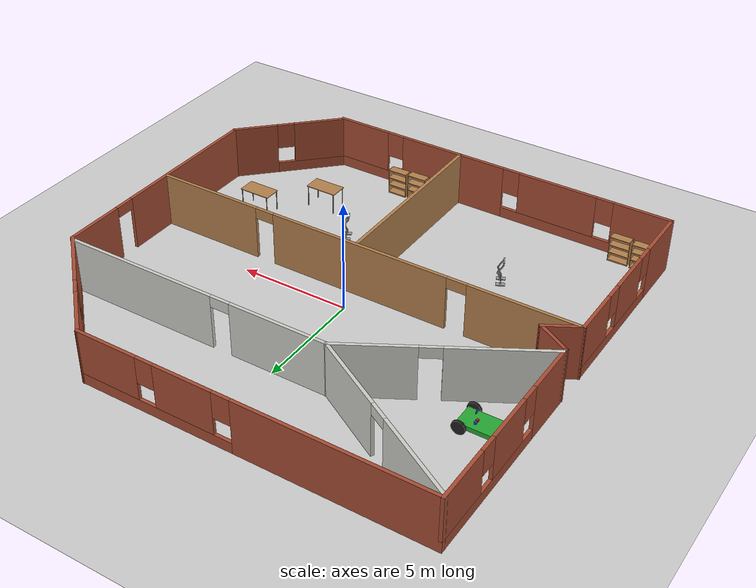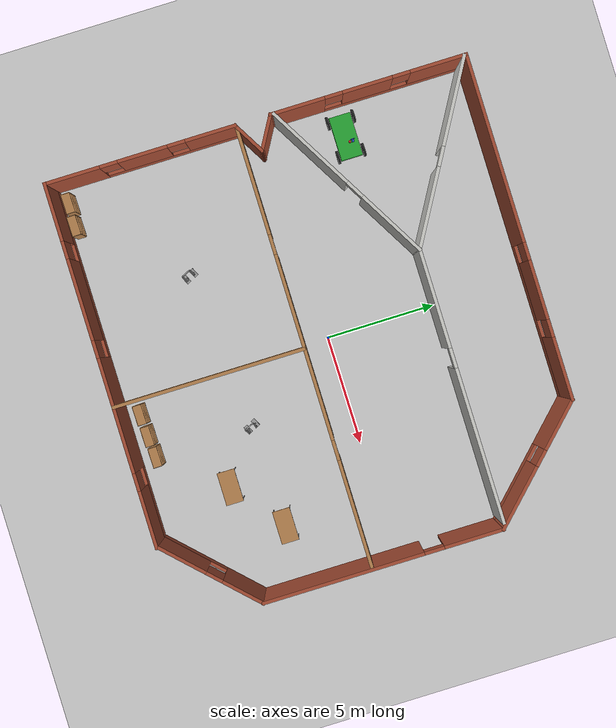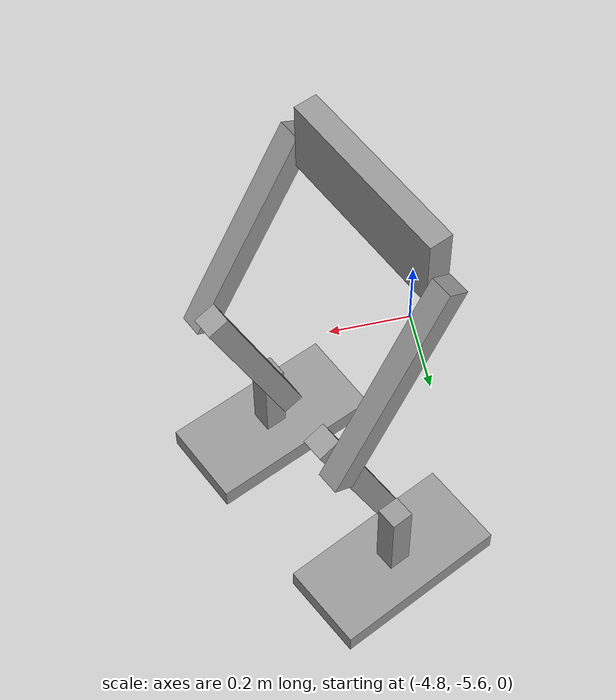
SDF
<sdf version="1.6">
 <world name="myworld">
  <light name="sun" type="directional">
   <pose>0 0 10 0 -0 0</pose>
   <diffuse>0.8 0.8 0.8 1</diffuse>
   <specular>0.1 0.1 0.1 1</specular>
   <attenuation>
    <range>1000</range>
    <constant>0.9</constant>
    <linear>0.01</linear>
    <quadratic>0.001</quadratic>
   </attenuation>
   <direction>-0.5 0.5 -1</direction>
  </light>
  <model name="ground_plane">
   <static>1</static>
   <link name="link">
    <collision name="collision">
     <geometry><plane><normal>0 0 1</normal><size>100 100</size></plane></geometry>
     <surface><friction><ode><mu>100</mu><mu2>50</mu2></ode></friction></surface>
    </collision>
    <visual name="visual">
     <cast_shadows>0</cast_shadows>
     <geometry><plane><normal>0 0 1</normal><size>100 100</size></plane></geometry>
     <material>
      <script><uri>file://media/materials/scripts/gazebo.material</uri><name>Gazebo/Grey</name></script>
     </material>
    </visual>
   </link>
  </model>
  <gravity>0 0 -9.8</gravity>
  <magnetic_field>6e-06 2.3e-05 -4.2e-05</magnetic_field>
  <atmosphere type="adiabatic"/>
  <physics name="default_physics" default="0" type="ode">
   <max_step_size>0.001</max_step_size>
   <real_time_factor>1</real_time_factor>
   <real_time_update_rate>1000</real_time_update_rate>
  </physics>
  <scene><ambient>0.4 0.4 0.4 1</ambient><background>0.7 0.7 0.7 1</background><shadows>1</shadows></scene>
  <spherical_coordinates>
   <surface_model>EARTH_WGS84</surface_model>
   <latitude_deg>0</latitude_deg>
   <longitude_deg>0</longitude_deg>
   <elevation>0</elevation>
   <heading_deg>0</heading_deg>
  </spherical_coordinates>
  <model name="hy_0">
   <pose>0.09983 -0.23319 0 0 -0 0</pose>
   <link name="Wall_12">
    <pose>-6.30136 2.96516 0 0 -0 0.523599</pose>
    <visual name="Wall_12_Visual_0">
     <pose>-2.17493 0 1.25 0 -0 0</pose>
     <geometry><box><size>4.40014 0.15 2.5</size></box></geometry>
     <material>
      <script><uri>file://media/materials/scripts/gazebo.material</uri><name>Gazebo/CeilingTiled</name></script>
      <ambient>0 0.92549 0 1</ambient>
     </material>
     <meta><layer>0</layer></meta>
    </visual>
    <collision name="Wall_12_Collision_0">
     <geometry><box><size>4.40014 0.15 2.5</size></box></geometry>
     <pose>-2.17493 0 1.25 0 -0 0</pose>
    </collision>
    <visual name="Wall_12_Visual_1">
     <pose>2.65007 0 1.25 0 -0 0</pose>
     <geometry><box><size>3.44986 0.15 2.5</size></box></geometry>
     <material>
      <script><uri>file://media/materials/scripts/gazebo.material</uri><name>Gazebo/CeilingTiled</name></script>
      <ambient>0 0.92549 0 1</ambient>
     </material>
     <meta><layer>0</layer></meta>
    </visual>
    <collision name="Wall_12_Collision_1">
     <geometry><box><size>3.44986 0.15 2.5</size></box></geometry>
     <pose>2.65007 0 1.25 0 -0 0</pose>
    </collision>
    <visual name="Wall_12_Visual_2">
     <pose>0.475144 0 2.25 0 -0 0</pose>
     <geometry><box><size>0.9 0.15 0.5</size></box></geometry>
     <material>
      <script><uri>file://media/materials/scripts/gazebo.material</uri><name>Gazebo/CeilingTiled</name></script>
      <ambient>0 0.92549 0 1</ambient>
     </material>
     <meta><layer>0</layer></meta>
    </visual>
    <collision name="Wall_12_Collision_2">
     <geometry><box><size>0.9 0.15 0.5</size></box></geometry>
     <pose>0.475144 0 2.25 0 -0 0</pose>
    </collision>
   </link>
   <link name="Wall_13">
    <pose>3.59755 5.11516 0 0 -0 0</pose>
    <visual name="Wall_13_Visual_0">
     <pose>-3.98409 0 1.25 0 -0 0</pose>
     <geometry><box><size>4.53183 0.15 2.5</size></box></geometry>
     <material>
      <script><uri>file://media/materials/scripts/gazebo.material</uri><name>Gazebo/CeilingTiled</name></script>
      <ambient>0 0.92549 0 1</ambient>
     </material>
     <meta><layer>0</layer></meta>
    </visual>
    <collision name="Wall_13_Collision_0">
     <geometry><box><size>4.53183 0.15 2.5</size></box></geometry>
     <pose>-3.98409 0 1.25 0 -0 0</pose>
    </collision>
    <visual name="Wall_13_Visual_1">
     <pose>2.71591 0 1.25 0 -0 0</pose>
     <geometry><box><size>7.06817 0.15 2.5</size></box></geometry>
     <material>
      <script><uri>file://media/materials/scripts/gazebo.material</uri><name>Gazebo/CeilingTiled</name></script>
      <ambient>0 0.92549 0 1</ambient>
     </material>
     <meta><layer>0</layer></meta>
    </visual>
    <collision name="Wall_13_Collision_1">
     <geometry><box><size>7.06817 0.15 2.5</size></box></geometry>
     <pose>2.71591 0 1.25 0 -0 0</pose>
    </collision>
    <visual name="Wall_13_Visual_2">
     <pose>-1.26817 0 2.25 0 -0 0</pose>
     <geometry><box><size>0.9 0.15 0.5</size></box></geometry>
     <material>
      <script><uri>file://media/materials/scripts/gazebo.material</uri><name>Gazebo/CeilingTiled</name></script>
      <ambient>0 0.92549 0 1</ambient>
     </material>
     <meta><layer>0</layer></meta>
    </visual>
    <collision name="Wall_13_Collision_2">
     <geometry><box><size>0.9 0.15 0.5</size></box></geometry>
     <pose>-1.26817 0 2.25 0 -0 0</pose>
    </collision>
   </link>
   <link name="Wall_15">
    <pose>-6.30136 7.26516 0 0 -0 2.61799</pose>
    <visual name="Wall_15_Visual_0">
     <pose>-2.49521 0 1.25 0 -0 0</pose>
     <geometry><box><size>3.75958 0.15 2.5</size></box></geometry>
     <material>
      <script><uri>file://media/materials/scripts/gazebo.material</uri><name>Gazebo/CeilingTiled</name></script>
      <ambient>0 0.92549 0 1</ambient>
     </material>
     <meta><layer>0</layer></meta>
    </visual>
    <collision name="Wall_15_Collision_0">
     <geometry><box><size>3.75958 0.15 2.5</size></box></geometry>
     <pose>-2.49521 0 1.25 0 -0 0</pose>
    </collision>
    <visual name="Wall_15_Visual_1">
     <pose>2.32979 0 1.25 0 -0 0</pose>
     <geometry><box><size>4.09042 0.15 2.5</size></box></geometry>
     <material>
      <script><uri>file://media/materials/scripts/gazebo.material</uri><name>Gazebo/CeilingTiled</name></script>
      <ambient>0 0.92549 0 1</ambient>
     </material>
     <meta><layer>0</layer></meta>
    </visual>
    <collision name="Wall_15_Collision_1">
     <geometry><box><size>4.09042 0.15 2.5</size></box></geometry>
     <pose>2.32979 0 1.25 0 -0 0</pose>
    </collision>
    <visual name="Wall_15_Visual_2">
     <pose>-0.165419 0 2.25 0 -0 0</pose>
     <geometry><box><size>0.9 0.15 0.5</size></box></geometry>
     <material>
      <script><uri>file://media/materials/scripts/gazebo.material</uri><name>Gazebo/CeilingTiled</name></script>
      <ambient>0 0.92549 0 1</ambient>
     </material>
     <meta><layer>0</layer></meta>
    </visual>
    <collision name="Wall_15_Collision_2">
     <geometry><box><size>0.9 0.15 0.5</size></box></geometry>
     <pose>-0.165419 0 2.25 0 -0 0</pose>
    </collision>
   </link>
   <link name="Wall_17">
    <collision name="Wall_17_Collision">
     <geometry><box><size>8.75 0.15 2.5</size></box></geometry>
     <pose>0 0 1.25 0 -0 0</pose>
    </collision>
    <visual name="Wall_17_Visual">
     <pose>0 0 1.25 0 -0 0</pose>
     <geometry><box><size>8.75 0.15 2.5</size></box></geometry>
     <material>
      <script><uri>file://media/materials/scripts/gazebo.material</uri><name>Gazebo/Wood</name></script>
      <ambient>1 1 1 1</ambient>
     </material>
     <meta><layer>0</layer></meta>
    </visual>
    <pose>0.053129 -5.24053 0 0 0 -1.5708</pose>
   </link>
   <link name="Wall_19">
    <pose>-4.99687 -9.54053 0 0 -0 3.14159</pose>
    <visual name="Wall_19_Visual_0">
     <pose>-3.97378 0 1.25 0 -0 0</pose>
     <geometry><box><size>2.30244 0.15 2.5</size></box></geometry>
     <material>
      <script><uri>file://media/materials/scripts/gazebo.material</uri><name>Gazebo/Bricks</name></script>
      <ambient>1 1 1 1</ambient>
     </material>
     <meta><layer>0</layer></meta>
    </visual>
    <collision name="Wall_19_Collision_0">
     <geometry><box><size>2.30244 0.15 2.5</size></box></geometry>
     <pose>-3.97378 0 1.25 0 -0 0</pose>
    </collision>
    <visual name="Wall_19_Visual_1">
     <pose>1.15122 0 0.25 0 -0 0</pose>
     <geometry><box><size>7.94756 0.15 0.5</size></box></geometry>
     <material>
      <script><uri>file://media/materials/scripts/gazebo.material</uri><name>Gazebo/Bricks</name></script>
      <ambient>1 1 1 1</ambient>
     </material>
     <meta><layer>0</layer></meta>
    </visual>
    <collision name="Wall_19_Collision_1">
     <geometry><box><size>7.94756 0.15 0.5</size></box></geometry>
     <pose>1.15122 0 0.25 0 -0 0</pose>
    </collision>
    <visual name="Wall_19_Visual_2">
     <pose>-0.178896 0 1.5 0 -0 0</pose>
     <geometry><box><size>3.68734 0.15 2</size></box></geometry>
     <material>
      <script><uri>file://media/materials/scripts/gazebo.material</uri><name>Gazebo/Bricks</name></script>
      <ambient>1 1 1 1</ambient>
     </material>
     <meta><layer>0</layer></meta>
    </visual>
    <collision name="Wall_19_Collision_2">
     <geometry><box><size>3.68734 0.15 2</size></box></geometry>
     <pose>-0.178896 0 1.5 0 -0 0</pose>
    </collision>
    <visual name="Wall_19_Visual_3">
     <pose>3.79489 0 1.5 0 -0 0</pose>
     <geometry><box><size>2.66023 0.15 2</size></box></geometry>
     <material>
      <script><uri>file://media/materials/scripts/gazebo.material</uri><name>Gazebo/Bricks</name></script>
      <ambient>1 1 1 1</ambient>
     </material>
     <meta><layer>0</layer></meta>
    </visual>
    <collision name="Wall_19_Collision_3">
     <geometry><box><size>2.66023 0.15 2</size></box></geometry>
     <pose>3.79489 0 1.5 0 -0 0</pose>
    </collision>
    <visual name="Wall_19_Visual_4">
     <pose>-2.42257 0 1.9 0 -0 0</pose>
     <geometry><box><size>0.8 0.15 1.2</size></box></geometry>
     <material>
      <script><uri>file://media/materials/scripts/gazebo.material</uri><name>Gazebo/Bricks</name></script>
      <ambient>1 1 1 1</ambient>
     </material>
     <meta><layer>0</layer></meta>
    </visual>
    <collision name="Wall_19_Collision_4">
     <geometry><box><size>0.8 0.15 1.2</size></box></geometry>
     <pose>-2.42257 0 1.9 0 -0 0</pose>
    </collision>
    <visual name="Wall_19_Visual_5">
     <pose>2.06477 0 1.9 0 -0 0</pose>
     <geometry><box><size>0.8 0.15 1.2</size></box></geometry>
     <material>
      <script><uri>file://media/materials/scripts/gazebo.material</uri><name>Gazebo/Bricks</name></script>
      <ambient>1 1 1 1</ambient>
     </material>
     <meta><layer>0</layer></meta>
    </visual>
    <collision name="Wall_19_Collision_5">
     <geometry><box><size>0.8 0.15 1.2</size></box></geometry>
     <pose>2.06477 0 1.9 0 -0 0</pose>
    </collision>
   </link>
   <link name="Wall_20">
    <pose>-10.0469 -5.24053 0 0 -0 1.5708</pose>
    <visual name="Wall_20_Visual_0">
     <pose>-3.09642 0 1.25 0 -0 0</pose>
     <geometry><box><size>2.55716 0.15 2.5</size></box></geometry>
     <material>
      <script><uri>file://media/materials/scripts/gazebo.material</uri><name>Gazebo/Bricks</name></script>
      <ambient>1 1 1 1</ambient>
     </material>
     <meta><layer>0</layer></meta>
    </visual>
    <collision name="Wall_20_Collision_0">
     <geometry><box><size>2.55716 0.15 2.5</size></box></geometry>
     <pose>-3.09642 0 1.25 0 -0 0</pose>
    </collision>
    <visual name="Wall_20_Visual_1">
     <pose>1.27858 0 0.25 0 -0 0</pose>
     <geometry><box><size>6.19284 0.15 0.5</size></box></geometry>
     <material>
      <script><uri>file://media/materials/scripts/gazebo.material</uri><name>Gazebo/Bricks</name></script>
      <ambient>1 1 1 1</ambient>
     </material>
     <meta><layer>0</layer></meta>
    </visual>
    <collision name="Wall_20_Collision_1">
     <geometry><box><size>6.19284 0.15 0.5</size></box></geometry>
     <pose>1.27858 0 0.25 0 -0 0</pose>
    </collision>
    <visual name="Wall_20_Visual_2">
     <pose>0.108783 0 1.5 0 -0 0</pose>
     <geometry><box><size>2.25324 0.15 2</size></box></geometry>
     <material>
      <script><uri>file://media/materials/scripts/gazebo.material</uri><name>Gazebo/Bricks</name></script>
      <ambient>1 1 1 1</ambient>
     </material>
     <meta><layer>0</layer></meta>
    </visual>
    <collision name="Wall_20_Collision_2">
     <geometry><box><size>2.25324 0.15 2</size></box></geometry>
     <pose>0.108783 0 1.5 0 -0 0</pose>
    </collision>
    <visual name="Wall_20_Visual_3">
     <pose>3.2052 0 1.5 0 -0 0</pose>
     <geometry><box><size>2.3396 0.15 2</size></box></geometry>
     <material>
      <script><uri>file://media/materials/scripts/gazebo.material</uri><name>Gazebo/Bricks</name></script>
      <ambient>1 1 1 1</ambient>
     </material>
     <meta><layer>0</layer></meta>
    </visual>
    <collision name="Wall_20_Collision_3">
     <geometry><box><size>2.3396 0.15 2</size></box></geometry>
     <pose>3.2052 0 1.5 0 -0 0</pose>
    </collision>
    <visual name="Wall_20_Visual_4">
     <pose>-1.41784 0 1.9 0 -0 0</pose>
     <geometry><box><size>0.8 0.15 1.2</size></box></geometry>
     <material>
      <script><uri>file://media/materials/scripts/gazebo.material</uri><name>Gazebo/Bricks</name></script>
      <ambient>1 1 1 1</ambient>
     </material>
     <meta><layer>0</layer></meta>
    </visual>
    <collision name="Wall_20_Collision_4">
     <geometry><box><size>0.8 0.15 1.2</size></box></geometry>
     <pose>-1.41784 0 1.9 0 -0 0</pose>
    </collision>
    <visual name="Wall_20_Visual_5">
     <pose>1.6354 0 1.9 0 -0 0</pose>
     <geometry><box><size>0.8 0.15 1.2</size></box></geometry>
     <material>
      <script><uri>file://media/materials/scripts/gazebo.material</uri><name>Gazebo/Bricks</name></script>
      <ambient>1 1 1 1</ambient>
     </material>
     <meta><layer>0</layer></meta>
    </visual>
    <collision name="Wall_20_Collision_5">
     <geometry><box><size>0.8 0.15 1.2</size></box></geometry>
     <pose>1.6354 0 1.9 0 -0 0</pose>
    </collision>
   </link>
   <link name="Wall_21">
    <collision name="Wall_21_Collision">
     <geometry><box><size>1.75 0.15 2.5</size></box></geometry>
     <pose>0 0 1.25 0 -0 0</pose>
    </collision>
    <visual name="Wall_21_Visual">
     <pose>0 0 1.25 0 -0 0</pose>
     <geometry><box><size>1.75 0.15 2.5</size></box></geometry>
     <material>
      <script><uri>file://media/materials/scripts/gazebo.material</uri><name>Gazebo/Bricks</name></script>
      <ambient>1 1 1 1</ambient>
     </material>
     <meta><layer>0</layer></meta>
    </visual>
    <pose>-9.35405 -0.540533 0 0 -0 0.523599</pose>
   </link>
   <link name="Wall_24">
    <collision name="Wall_24_Collision">
     <geometry><box><size>1.75 0.15 2.5</size></box></geometry>
     <pose>0 0 1.25 0 -0 0</pose>
    </collision>
    <visual name="Wall_24_Visual">
     <pose>0 0 1.25 0 -0 0</pose>
     <geometry><box><size>1.75 0.15 2.5</size></box></geometry>
     <material>
      <script><uri>file://media/materials/scripts/gazebo.material</uri><name>Gazebo/Bricks</name></script>
      <ambient>1 1 1 1</ambient>
     </material>
     <meta><layer>0</layer></meta>
    </visual>
    <pose>-9.35405 0.259467 0 0 -0 2.61799</pose>
   </link>
   <link name="Wall_25">
    <pose>-10.0469 5.08447 0 0 -0 1.5708</pose>
    <visual name="Wall_25_Visual_0">
     <pose>-3.23269 0 1.25 0 -0 0</pose>
     <geometry><box><size>2.53463 0.15 2.5</size></box></geometry>
     <material>
      <script><uri>file://media/materials/scripts/gazebo.material</uri><name>Gazebo/Bricks</name></script>
      <ambient>1 1 1 1</ambient>
     </material>
     <meta><layer>0</layer></meta>
    </visual>
    <collision name="Wall_25_Collision_0">
     <geometry><box><size>2.53463 0.15 2.5</size></box></geometry>
     <pose>-3.23269 0 1.25 0 -0 0</pose>
    </collision>
    <visual name="Wall_25_Visual_1">
     <pose>1.26731 0 0.25 0 -0 0</pose>
     <geometry><box><size>6.46537 0.15 0.5</size></box></geometry>
     <material>
      <script><uri>file://media/materials/scripts/gazebo.material</uri><name>Gazebo/Bricks</name></script>
      <ambient>1 1 1 1</ambient>
     </material>
     <meta><layer>0</layer></meta>
    </visual>
    <collision name="Wall_25_Collision_1">
     <geometry><box><size>6.46537 0.15 0.5</size></box></geometry>
     <pose>1.26731 0 0.25 0 -0 0</pose>
    </collision>
    <visual name="Wall_25_Visual_2">
     <pose>-0.038749 0 1.5 0 -0 0</pose>
     <geometry><box><size>2.25324 0.15 2</size></box></geometry>
     <material>
      <script><uri>file://media/materials/scripts/gazebo.material</uri><name>Gazebo/Bricks</name></script>
      <ambient>1 1 1 1</ambient>
     </material>
     <meta><layer>0</layer></meta>
    </visual>
    <collision name="Wall_25_Collision_2">
     <geometry><box><size>2.25324 0.15 2</size></box></geometry>
     <pose>-0.038749 0 1.5 0 -0 0</pose>
    </collision>
    <visual name="Wall_25_Visual_3">
     <pose>3.19394 0 1.5 0 -0 0</pose>
     <geometry><box><size>2.61213 0.15 2</size></box></geometry>
     <material>
      <script><uri>file://media/materials/scripts/gazebo.material</uri><name>Gazebo/Bricks</name></script>
      <ambient>1 1 1 1</ambient>
     </material>
     <meta><layer>0</layer></meta>
    </visual>
    <collision name="Wall_25_Collision_3">
     <geometry><box><size>2.61213 0.15 2</size></box></geometry>
     <pose>3.19394 0 1.5 0 -0 0</pose>
    </collision>
    <visual name="Wall_25_Visual_4">
     <pose>-1.56537 0 1.9 0 -0 0</pose>
     <geometry><box><size>0.8 0.15 1.2</size></box></geometry>
     <material>
      <script><uri>file://media/materials/scripts/gazebo.material</uri><name>Gazebo/Bricks</name></script>
      <ambient>1 1 1 1</ambient>
     </material>
     <meta><layer>0</layer></meta>
    </visual>
    <collision name="Wall_25_Collision_4">
     <geometry><box><size>0.8 0.15 1.2</size></box></geometry>
     <pose>-1.56537 0 1.9 0 -0 0</pose>
    </collision>
    <visual name="Wall_25_Visual_5">
     <pose>1.48787 0 1.9 0 -0 0</pose>
     <geometry><box><size>0.8 0.15 1.2</size></box></geometry>
     <material>
      <script><uri>file://media/materials/scripts/gazebo.material</uri><name>Gazebo/Bricks</name></script>
      <ambient>1 1 1 1</ambient>
     </material>
     <meta><layer>0</layer></meta>
    </visual>
    <collision name="Wall_25_Collision_5">
     <geometry><box><size>0.8 0.15 1.2</size></box></geometry>
     <pose>1.48787 0 1.9 0 -0 0</pose>
    </collision>
   </link>
   <link name="Wall_26">
    <pose>-2.24687 9.50947 0 0 -0 0</pose>
    <visual name="Wall_26_Visual_0">
     <pose>-3.58997 0 1.25 0 -0 0</pose>
     <geometry><box><size>8.57005 0.15 2.5</size></box></geometry>
     <material>
      <script><uri>file://media/materials/scripts/gazebo.material</uri><name>Gazebo/Bricks</name></script>
      <ambient>1 1 1 1</ambient>
     </material>
     <meta><layer>0</layer></meta>
    </visual>
    <collision name="Wall_26_Collision_0">
     <geometry><box><size>8.57005 0.15 2.5</size></box></geometry>
     <pose>-3.58997 0 1.25 0 -0 0</pose>
    </collision>
    <visual name="Wall_26_Visual_1">
     <pose>4.28503 0 0.25 0 -0 0</pose>
     <geometry><box><size>7.17995 0.15 0.5</size></box></geometry>
     <material>
      <script><uri>file://media/materials/scripts/gazebo.material</uri><name>Gazebo/Bricks</name></script>
      <ambient>1 1 1 1</ambient>
     </material>
     <meta><layer>0</layer></meta>
    </visual>
    <collision name="Wall_26_Collision_1">
     <geometry><box><size>7.17995 0.15 0.5</size></box></geometry>
     <pose>4.28503 0 0.25 0 -0 0</pose>
    </collision>
    <visual name="Wall_26_Visual_2">
     <pose>2.83747 0 1.5 0 -0 0</pose>
     <geometry><box><size>2.68484 0.15 2</size></box></geometry>
     <material>
      <script><uri>file://media/materials/scripts/gazebo.material</uri><name>Gazebo/Bricks</name></script>
      <ambient>1 1 1 1</ambient>
     </material>
     <meta><layer>0</layer></meta>
    </visual>
    <collision name="Wall_26_Collision_2">
     <geometry><box><size>2.68484 0.15 2</size></box></geometry>
     <pose>2.83747 0 1.5 0 -0 0</pose>
    </collision>
    <visual name="Wall_26_Visual_3">
     <pose>6.42744 0 1.5 0 -0 0</pose>
     <geometry><box><size>2.89511 0.15 2</size></box></geometry>
     <material>
      <script><uri>file://media/materials/scripts/gazebo.material</uri><name>Gazebo/Bricks</name></script>
      <ambient>1 1 1 1</ambient>
     </material>
     <meta><layer>0</layer></meta>
    </visual>
    <collision name="Wall_26_Collision_3">
     <geometry><box><size>2.89511 0.15 2</size></box></geometry>
     <pose>6.42744 0 1.5 0 -0 0</pose>
    </collision>
    <visual name="Wall_26_Visual_4">
     <pose>1.09505 0 1.9 0 -0 0</pose>
     <geometry><box><size>0.8 0.15 1.2</size></box></geometry>
     <material>
      <script><uri>file://media/materials/scripts/gazebo.material</uri><name>Gazebo/Bricks</name></script>
      <ambient>1 1 1 1</ambient>
     </material>
     <meta><layer>0</layer></meta>
    </visual>
    <collision name="Wall_26_Collision_4">
     <geometry><box><size>0.8 0.15 1.2</size></box></geometry>
     <pose>1.09505 0 1.9 0 -0 0</pose>
    </collision>
    <visual name="Wall_26_Visual_5">
     <pose>4.57989 0 1.9 0 -0 0</pose>
     <geometry><box><size>0.8 0.15 1.2</size></box></geometry>
     <material>
      <script><uri>file://media/materials/scripts/gazebo.material</uri><name>Gazebo/Bricks</name></script>
      <ambient>1 1 1 1</ambient>
     </material>
     <meta><layer>0</layer></meta>
    </visual>
    <collision name="Wall_26_Collision_5">
     <geometry><box><size>0.8 0.15 1.2</size></box></geometry>
     <pose>4.57989 0 1.9 0 -0 0</pose>
    </collision>
   </link>
   <link name="Wall_27">
    <pose>7.79819 7.2644 0 0 0 -0.785398</pose>
    <visual name="Wall_27_Visual_0">
     <pose>-1.97639 0 1.25 0 -0 0</pose>
     <geometry><box><size>2.54722 0.15 2.5</size></box></geometry>
     <material>
      <script><uri>file://media/materials/scripts/gazebo.material</uri><name>Gazebo/Bricks</name></script>
      <ambient>1 1 1 1</ambient>
     </material>
     <meta><layer>0</layer></meta>
    </visual>
    <collision name="Wall_27_Collision_0">
     <geometry><box><size>2.54722 0.15 2.5</size></box></geometry>
     <pose>-1.97639 0 1.25 0 -0 0</pose>
    </collision>
    <visual name="Wall_27_Visual_1">
     <pose>1.27361 0 0.25 0 -0 0</pose>
     <geometry><box><size>3.95278 0.15 0.5</size></box></geometry>
     <material>
      <script><uri>file://media/materials/scripts/gazebo.material</uri><name>Gazebo/Bricks</name></script>
      <ambient>1 1 1 1</ambient>
     </material>
     <meta><layer>0</layer></meta>
    </visual>
    <collision name="Wall_27_Collision_1">
     <geometry><box><size>3.95278 0.15 0.5</size></box></geometry>
     <pose>1.27361 0 0.25 0 -0 0</pose>
    </collision>
    <visual name="Wall_27_Visual_2">
     <pose>1.67361 0 1.5 0 -0 0</pose>
     <geometry><box><size>3.15278 0.15 2</size></box></geometry>
     <material>
      <script><uri>file://media/materials/scripts/gazebo.material</uri><name>Gazebo/Bricks</name></script>
      <ambient>1 1 1 1</ambient>
     </material>
     <meta><layer>0</layer></meta>
    </visual>
    <collision name="Wall_27_Collision_2">
     <geometry><box><size>3.15278 0.15 2</size></box></geometry>
     <pose>1.67361 0 1.5 0 -0 0</pose>
    </collision>
    <visual name="Wall_27_Visual_3">
     <pose>-0.302777 0 1.9 0 -0 0</pose>
     <geometry><box><size>0.8 0.15 1.2</size></box></geometry>
     <material>
      <script><uri>file://media/materials/scripts/gazebo.material</uri><name>Gazebo/Bricks</name></script>
      <ambient>1 1 1 1</ambient>
     </material>
     <meta><layer>0</layer></meta>
    </visual>
    <collision name="Wall_27_Collision_3">
     <geometry><box><size>0.8 0.15 1.2</size></box></geometry>
     <pose>-0.302777 0 1.9 0 -0 0</pose>
    </collision>
   </link>
   <link name="Wall_28">
    <pose>10.0433 -0.405662 0 0 0 -1.5708</pose>
    <visual name="Wall_28_Visual_0">
     <pose>-4.12781 0 1.25 0 -0 0</pose>
     <geometry><box><size>2.74438 0.15 2.5</size></box></geometry>
     <material>
      <script><uri>file://media/materials/scripts/gazebo.material</uri><name>Gazebo/Bricks</name></script>
      <ambient>1 1 1 1</ambient>
     </material>
     <meta><layer>0</layer></meta>
    </visual>
    <collision name="Wall_28_Collision_0">
     <geometry><box><size>2.74438 0.15 2.5</size></box></geometry>
     <pose>-4.12781 0 1.25 0 -0 0</pose>
    </collision>
    <visual name="Wall_28_Visual_1">
     <pose>1.82219 0 1.25 0 -0 0</pose>
     <geometry><box><size>7.35562 0.15 2.5</size></box></geometry>
     <material>
      <script><uri>file://media/materials/scripts/gazebo.material</uri><name>Gazebo/Bricks</name></script>
      <ambient>1 1 1 1</ambient>
     </material>
     <meta><layer>0</layer></meta>
    </visual>
    <collision name="Wall_28_Collision_1">
     <geometry><box><size>7.35562 0.15 2.5</size></box></geometry>
     <pose>1.82219 0 1.25 0 -0 0</pose>
    </collision>
    <visual name="Wall_28_Visual_2">
     <pose>-2.30562 0 2.25 0 -0 0</pose>
     <geometry><box><size>0.9 0.15 0.5</size></box></geometry>
     <material>
      <script><uri>file://media/materials/scripts/gazebo.material</uri><name>Gazebo/Bricks</name></script>
      <ambient>1 1 1 1</ambient>
     </material>
     <meta><layer>0</layer></meta>
    </visual>
    <collision name="Wall_28_Collision_2">
     <geometry><box><size>0.9 0.15 0.5</size></box></geometry>
     <pose>-2.30562 0 2.25 0 -0 0</pose>
    </collision>
   </link>
   <link name="Wall_29">
    <pose>8.24014 -7.63378 0 0 0 -2.35619</pose>
    <visual name="Wall_29_Visual_0">
     <pose>-1.58309 0 1.25 0 -0 0</pose>
     <geometry><box><size>2.08382 0.15 2.5</size></box></geometry>
     <material>
      <script><uri>file://media/materials/scripts/gazebo.material</uri><name>Gazebo/Bricks</name></script>
      <ambient>1 1 1 1</ambient>
     </material>
     <meta><layer>0</layer></meta>
    </visual>
    <collision name="Wall_29_Collision_0">
     <geometry><box><size>2.08382 0.15 2.5</size></box></geometry>
     <pose>-1.58309 0 1.25 0 -0 0</pose>
    </collision>
    <visual name="Wall_29_Visual_1">
     <pose>1.04191 0 0.25 0 -0 0</pose>
     <geometry><box><size>3.16618 0.15 0.5</size></box></geometry>
     <material>
      <script><uri>file://media/materials/scripts/gazebo.material</uri><name>Gazebo/Bricks</name></script>
      <ambient>1 1 1 1</ambient>
     </material>
     <meta><layer>0</layer></meta>
    </visual>
    <collision name="Wall_29_Collision_1">
     <geometry><box><size>3.16618 0.15 0.5</size></box></geometry>
     <pose>1.04191 0 0.25 0 -0 0</pose>
    </collision>
    <visual name="Wall_29_Visual_2">
     <pose>1.44191 0 1.5 0 -0 0</pose>
     <geometry><box><size>2.36618 0.15 2</size></box></geometry>
     <material>
      <script><uri>file://media/materials/scripts/gazebo.material</uri><name>Gazebo/Bricks</name></script>
      <ambient>1 1 1 1</ambient>
     </material>
     <meta><layer>0</layer></meta>
    </visual>
    <collision name="Wall_29_Collision_2">
     <geometry><box><size>2.36618 0.15 2</size></box></geometry>
     <pose>1.44191 0 1.5 0 -0 0</pose>
    </collision>
    <visual name="Wall_29_Visual_3">
     <pose>-0.141178 0 1.9 0 -0 0</pose>
     <geometry><box><size>0.8 0.15 1.2</size></box></geometry>
     <material>
      <script><uri>file://media/materials/scripts/gazebo.material</uri><name>Gazebo/Bricks</name></script>
      <ambient>1 1 1 1</ambient>
     </material>
     <meta><layer>0</layer></meta>
    </visual>
    <collision name="Wall_29_Collision_3">
     <geometry><box><size>0.8 0.15 1.2</size></box></geometry>
     <pose>-0.141178 0 1.9 0 -0 0</pose>
    </collision>
   </link>
   <link name="Wall_31">
    <pose>3.22813 -9.54053 0 0 -0 0</pose>
    <visual name="Wall_31_Visual_0">
     <pose>-1.71924 0 1.25 0 -0 0</pose>
     <geometry><box><size>3.06152 0.15 2.5</size></box></geometry>
     <material>
      <script><uri>file://media/materials/scripts/gazebo.material</uri><name>Gazebo/Bricks</name></script>
      <ambient>1 1 1 1</ambient>
     </material>
     <meta><layer>0</layer></meta>
    </visual>
    <collision name="Wall_31_Collision_0">
     <geometry><box><size>3.06152 0.15 2.5</size></box></geometry>
     <pose>-1.71924 0 1.25 0 -0 0</pose>
    </collision>
    <visual name="Wall_31_Visual_1">
     <pose>1.53076 0 0.25 0 -0 0</pose>
     <geometry><box><size>3.43848 0.15 0.5</size></box></geometry>
     <material>
      <script><uri>file://media/materials/scripts/gazebo.material</uri><name>Gazebo/Bricks</name></script>
      <ambient>1 1 1 1</ambient>
     </material>
     <meta><layer>0</layer></meta>
    </visual>
    <collision name="Wall_31_Collision_1">
     <geometry><box><size>3.43848 0.15 0.5</size></box></geometry>
     <pose>1.53076 0 0.25 0 -0 0</pose>
    </collision>
    <visual name="Wall_31_Visual_2">
     <pose>1.93076 0 1.5 0 -0 0</pose>
     <geometry><box><size>2.63848 0.15 2</size></box></geometry>
     <material>
      <script><uri>file://media/materials/scripts/gazebo.material</uri><name>Gazebo/Bricks</name></script>
      <ambient>1 1 1 1</ambient>
     </material>
     <meta><layer>0</layer></meta>
    </visual>
    <collision name="Wall_31_Collision_2">
     <geometry><box><size>2.63848 0.15 2</size></box></geometry>
     <pose>1.93076 0 1.5 0 -0 0</pose>
    </collision>
    <visual name="Wall_31_Visual_3">
     <pose>0.211523 0 1.9 0 -0 0</pose>
     <geometry><box><size>0.8 0.15 1.2</size></box></geometry>
     <material>
      <script><uri>file://media/materials/scripts/gazebo.material</uri><name>Gazebo/Bricks</name></script>
      <ambient>1 1 1 1</ambient>
     </material>
     <meta><layer>0</layer></meta>
    </visual>
    <collision name="Wall_31_Collision_3">
     <geometry><box><size>0.8 0.15 1.2</size></box></geometry>
     <pose>0.211523 0 1.9 0 -0 0</pose>
    </collision>
   </link>
   <link name="Wall_7">
    <pose>0.05386 -0.903715 0 0 -0 0</pose>
    <visual name="Wall_7_Visual_0">
     <pose>-7.57996 0 1.25 0 -0 0</pose>
     <geometry><box><size>4.84008 0.15 2.5</size></box></geometry>
     <material>
      <script><uri>file://media/materials/scripts/gazebo.material</uri><name>Gazebo/Wood</name></script>
      <ambient>1 1 1 1</ambient>
     </material>
     <meta><layer>0</layer></meta>
    </visual>
    <collision name="Wall_7_Collision_0">
     <geometry><box><size>4.84008 0.15 2.5</size></box></geometry>
     <pose>-7.57996 0 1.25 0 -0 0</pose>
    </collision>
    <visual name="Wall_7_Visual_1">
     <pose>-0.060669 0 1.25 0 -0 0</pose>
     <geometry><box><size>8.3985 0.15 2.5</size></box></geometry>
     <material>
      <script><uri>file://media/materials/scripts/gazebo.material</uri><name>Gazebo/Wood</name></script>
      <ambient>1 1 1 1</ambient>
     </material>
     <meta><layer>0</layer></meta>
    </visual>
    <collision name="Wall_7_Collision_1">
     <geometry><box><size>8.3985 0.15 2.5</size></box></geometry>
     <pose>-0.060669 0 1.25 0 -0 0</pose>
    </collision>
    <visual name="Wall_7_Visual_2">
     <pose>7.51929 0 1.25 0 -0 0</pose>
     <geometry><box><size>4.96142 0.15 2.5</size></box></geometry>
     <material>
      <script><uri>file://media/materials/scripts/gazebo.material</uri><name>Gazebo/Wood</name></script>
      <ambient>1 1 1 1</ambient>
     </material>
     <meta><layer>0</layer></meta>
    </visual>
    <collision name="Wall_7_Collision_2">
     <geometry><box><size>4.96142 0.15 2.5</size></box></geometry>
     <pose>7.51929 0 1.25 0 -0 0</pose>
    </collision>
    <visual name="Wall_7_Visual_3">
     <pose>-4.70992 0 2.25 0 -0 0</pose>
     <geometry><box><size>0.9 0.15 0.5</size></box></geometry>
     <material>
      <script><uri>file://media/materials/scripts/gazebo.material</uri><name>Gazebo/Wood</name></script>
      <ambient>1 1 1 1</ambient>
     </material>
     <meta><layer>0</layer></meta>
    </visual>
    <collision name="Wall_7_Collision_3">
     <geometry><box><size>0.9 0.15 0.5</size></box></geometry>
     <pose>-4.70992 0 2.25 0 -0 0</pose>
    </collision>
    <visual name="Wall_7_Visual_4">
     <pose>4.58858 0 2.25 0 -0 0</pose>
     <geometry><box><size>0.9 0.15 0.5</size></box></geometry>
     <material>
      <script><uri>file://media/materials/scripts/gazebo.material</uri><name>Gazebo/Wood</name></script>
      <ambient>1 1 1 1</ambient>
     </material>
     <meta><layer>0</layer></meta>
    </visual>
    <collision name="Wall_7_Collision_4">
     <geometry><box><size>0.9 0.15 0.5</size></box></geometry>
     <pose>4.58858 0 2.25 0 -0 0</pose>
    </collision>
   </link>
   <static>1</static>
  </model>
  <model name="bookshelf">
   <static>1</static>
   <link name="link">
    <inertial><mass>1</mass></inertial>
    <collision name="back">
     <pose>0 0.005 0.6 0 -0 0</pose>
     <geometry><box><size>0.9 0.01 1.2</size></box></geometry>
    </collision>
    <visual name="visual1">
     <pose>0 0.005 0.6 0 -0 0</pose>
     <geometry><box><size>0.9 0.01 1.2</size></box></geometry>
     <material>
      <script><uri>file://media/materials/scripts/gazebo.material</uri><name>Gazebo/Wood</name></script>
     </material>
    </visual>
    <collision name="left_side">
     <pose>0.45 -0.195 0.6 0 -0 0</pose>
     <geometry><box><size>0.02 0.4 1.2</size></box></geometry>
    </collision>
    <visual name="visual2">
     <pose>0.45 -0.195 0.6 0 -0 0</pose>
     <geometry><box><size>0.02 0.4 1.2</size></box></geometry>
     <material>
      <script><uri>file://media/materials/scripts/gazebo.material</uri><name>Gazebo/Wood</name></script>
     </material>
    </visual>
    <collision name="right_side">
     <pose>-0.45 -0.195 0.6 0 -0 0</pose>
     <geometry><box><size>0.02 0.4 1.2</size></box></geometry>
    </collision>
    <visual name="visual3">
     <pose>-0.45 -0.195 0.6 0 -0 0</pose>
     <geometry><box><size>0.02 0.4 1.2</size></box></geometry>
     <material>
      <script><uri>file://media/materials/scripts/gazebo.material</uri><name>Gazebo/Wood</name></script>
     </material>
    </visual>
    <collision name="bottom">
     <pose>0 -0.195 0.03 0 -0 0</pose>
     <geometry><box><size>0.88 0.4 0.06</size></box></geometry>
    </collision>
    <visual name="visual4">
     <pose>0 -0.195 0.03 0 -0 0</pose>
     <geometry><box><size>0.88 0.4 0.06</size></box></geometry>
     <material>
      <script><uri>file://media/materials/scripts/gazebo.material</uri><name>Gazebo/Wood</name></script>
     </material>
    </visual>
    <collision name="top">
     <pose>0 -0.195 1.19 0 -0 0</pose>
     <geometry><box><size>0.88 0.4 0.02</size></box></geometry>
    </collision>
    <visual name="visual5">
     <pose>0 -0.195 1.19 0 -0 0</pose>
     <geometry><box><size>0.88 0.4 0.02</size></box></geometry>
     <material>
      <script><uri>file://media/materials/scripts/gazebo.material</uri><name>Gazebo/Wood</name></script>
     </material>
    </visual>
    <collision name="low_shelf">
     <pose>0 -0.195 0.43 0 -0 0</pose>
     <geometry><box><size>0.88 0.4 0.02</size></box></geometry>
    </collision>
    <visual name="visual6">
     <pose>0 -0.195 0.43 0 -0 0</pose>
     <geometry><box><size>0.88 0.4 0.02</size></box></geometry>
     <material>
      <script><uri>file://media/materials/scripts/gazebo.material</uri><name>Gazebo/Wood</name></script>
     </material>
    </visual>
    <collision name="high_shelf">
     <pose>0 -0.195 0.8 0 -0 0</pose>
     <geometry><box><size>0.88 0.4 0.02</size></box></geometry>
    </collision>
    <visual name="visual7">
     <pose>0 -0.195 0.8 0 -0 0</pose>
     <geometry><box><size>0.88 0.4 0.02</size></box></geometry>
     <material>
      <script><uri>file://media/materials/scripts/gazebo.material</uri><name>Gazebo/Wood</name></script>
     </material>
    </visual>
   </link>
   <pose>0.833883 -9.23444 0 0 0 -3.1294</pose>
  </model>
  <model name="bookshelf_clone">
   <static>1</static>
   <link name="link">
    <inertial><mass>1</mass></inertial>
    <collision name="back">
     <pose>0 0.005 0.6 0 -0 0</pose>
     <geometry><box><size>0.9 0.01 1.2</size></box></geometry>
    </collision>
    <visual name="visual1">
     <pose>0 0.005 0.6 0 -0 0</pose>
     <geometry><box><size>0.9 0.01 1.2</size></box></geometry>
     <material>
      <script><uri>file://media/materials/scripts/gazebo.material</uri><name>Gazebo/Wood</name></script>
     </material>
    </visual>
    <collision name="left_side">
     <pose>0.45 -0.195 0.6 0 -0 0</pose>
     <geometry><box><size>0.02 0.4 1.2</size></box></geometry>
    </collision>
    <visual name="visual2">
     <pose>0.45 -0.195 0.6 0 -0 0</pose>
     <geometry><box><size>0.02 0.4 1.2</size></box></geometry>
     <material>
      <script><uri>file://media/materials/scripts/gazebo.material</uri><name>Gazebo/Wood</name></script>
     </material>
    </visual>
    <collision name="right_side">
     <pose>-0.45 -0.195 0.6 0 -0 0</pose>
     <geometry><box><size>0.02 0.4 1.2</size></box></geometry>
    </collision>
    <visual name="visual3">
     <pose>-0.45 -0.195 0.6 0 -0 0</pose>
     <geometry><box><size>0.02 0.4 1.2</size></box></geometry>
     <material>
      <script><uri>file://media/materials/scripts/gazebo.material</uri><name>Gazebo/Wood</name></script>
     </material>
    </visual>
    <collision name="bottom">
     <pose>0 -0.195 0.03 0 -0 0</pose>
     <geometry><box><size>0.88 0.4 0.06</size></box></geometry>
    </collision>
    <visual name="visual4">
     <pose>0 -0.195 0.03 0 -0 0</pose>
     <geometry><box><size>0.88 0.4 0.06</size></box></geometry>
     <material>
      <script><uri>file://media/materials/scripts/gazebo.material</uri><name>Gazebo/Wood</name></script>
     </material>
    </visual>
    <collision name="top">
     <pose>0 -0.195 1.19 0 -0 0</pose>
     <geometry><box><size>0.88 0.4 0.02</size></box></geometry>
    </collision>
    <visual name="visual5">
     <pose>0 -0.195 1.19 0 -0 0</pose>
     <geometry><box><size>0.88 0.4 0.02</size></box></geometry>
     <material>
      <script><uri>file://media/materials/scripts/gazebo.material</uri><name>Gazebo/Wood</name></script>
     </material>
    </visual>
    <collision name="low_shelf">
     <pose>0 -0.195 0.43 0 -0 0</pose>
     <geometry><box><size>0.88 0.4 0.02</size></box></geometry>
    </collision>
    <visual name="visual6">
     <pose>0 -0.195 0.43 0 -0 0</pose>
     <geometry><box><size>0.88 0.4 0.02</size></box></geometry>
     <material>
      <script><uri>file://media/materials/scripts/gazebo.material</uri><name>Gazebo/Wood</name></script>
     </material>
    </visual>
    <collision name="high_shelf">
     <pose>0 -0.195 0.8 0 -0 0</pose>
     <geometry><box><size>0.88 0.4 0.02</size></box></geometry>
    </collision>
    <visual name="visual7">
     <pose>0 -0.195 0.8 0 -0 0</pose>
     <geometry><box><size>0.88 0.4 0.02</size></box></geometry>
     <material>
      <script><uri>file://media/materials/scripts/gazebo.material</uri><name>Gazebo/Wood</name></script>
     </material>
    </visual>
   </link>
   <pose>-9.09492 -9.49507 0 0 0 -3.1294</pose>
  </model>
  <model name="bookshelf_clone_0">
   <static>1</static>
   <link name="link">
    <inertial><mass>1</mass></inertial>
    <collision name="back">
     <pose>0 0.005 0.6 0 -0 0</pose>
     <geometry><box><size>0.9 0.01 1.2</size></box></geometry>
    </collision>
    <visual name="visual1">
     <pose>0 0.005 0.6 0 -0 0</pose>
     <geometry><box><size>0.9 0.01 1.2</size></box></geometry>
     <material>
      <script><uri>file://media/materials/scripts/gazebo.material</uri><name>Gazebo/Wood</name></script>
     </material>
    </visual>
    <collision name="left_side">
     <pose>0.45 -0.195 0.6 0 -0 0</pose>
     <geometry><box><size>0.02 0.4 1.2</size></box></geometry>
    </collision>
    <visual name="visual2">
     <pose>0.45 -0.195 0.6 0 -0 0</pose>
     <geometry><box><size>0.02 0.4 1.2</size></box></geometry>
     <material>
      <script><uri>file://media/materials/scripts/gazebo.material</uri><name>Gazebo/Wood</name></script>
     </material>
    </visual>
    <collision name="right_side">
     <pose>-0.45 -0.195 0.6 0 -0 0</pose>
     <geometry><box><size>0.02 0.4 1.2</size></box></geometry>
    </collision>
    <visual name="visual3">
     <pose>-0.45 -0.195 0.6 0 -0 0</pose>
     <geometry><box><size>0.02 0.4 1.2</size></box></geometry>
     <material>
      <script><uri>file://media/materials/scripts/gazebo.material</uri><name>Gazebo/Wood</name></script>
     </material>
    </visual>
    <collision name="bottom">
     <pose>0 -0.195 0.03 0 -0 0</pose>
     <geometry><box><size>0.88 0.4 0.06</size></box></geometry>
    </collision>
    <visual name="visual4">
     <pose>0 -0.195 0.03 0 -0 0</pose>
     <geometry><box><size>0.88 0.4 0.06</size></box></geometry>
     <material>
      <script><uri>file://media/materials/scripts/gazebo.material</uri><name>Gazebo/Wood</name></script>
     </material>
    </visual>
    <collision name="top">
     <pose>0 -0.195 1.19 0 -0 0</pose>
     <geometry><box><size>0.88 0.4 0.02</size></box></geometry>
    </collision>
    <visual name="visual5">
     <pose>0 -0.195 1.19 0 -0 0</pose>
     <geometry><box><size>0.88 0.4 0.02</size></box></geometry>
     <material>
      <script><uri>file://media/materials/scripts/gazebo.material</uri><name>Gazebo/Wood</name></script>
     </material>
    </visual>
    <collision name="low_shelf">
     <pose>0 -0.195 0.43 0 -0 0</pose>
     <geometry><box><size>0.88 0.4 0.02</size></box></geometry>
    </collision>
    <visual name="visual6">
     <pose>0 -0.195 0.43 0 -0 0</pose>
     <geometry><box><size>0.88 0.4 0.02</size></box></geometry>
     <material>
      <script><uri>file://media/materials/scripts/gazebo.material</uri><name>Gazebo/Wood</name></script>
     </material>
    </visual>
    <collision name="high_shelf">
     <pose>0 -0.195 0.8 0 -0 0</pose>
     <geometry><box><size>0.88 0.4 0.02</size></box></geometry>
    </collision>
    <visual name="visual7">
     <pose>0 -0.195 0.8 0 -0 0</pose>
     <geometry><box><size>0.88 0.4 0.02</size></box></geometry>
     <material>
      <script><uri>file://media/materials/scripts/gazebo.material</uri><name>Gazebo/Wood</name></script>
     </material>
    </visual>
   </link>
   <pose>1.84603 -9.18341 0 0 0 -3.1294</pose>
  </model>
  <model name="bookshelf_clone_1">
   <static>1</static>
   <link name="link">
    <inertial><mass>1</mass></inertial>
    <collision name="back">
     <pose>0 0.005 0.6 0 -0 0</pose>
     <geometry><box><size>0.9 0.01 1.2</size></box></geometry>
    </collision>
    <visual name="visual1">
     <pose>0 0.005 0.6 0 -0 0</pose>
     <geometry><box><size>0.9 0.01 1.2</size></box></geometry>
     <material>
      <script><uri>file://media/materials/scripts/gazebo.material</uri><name>Gazebo/Wood</name></script>
     </material>
    </visual>
    <collision name="left_side">
     <pose>0.45 -0.195 0.6 0 -0 0</pose>
     <geometry><box><size>0.02 0.4 1.2</size></box></geometry>
    </collision>
    <visual name="visual2">
     <pose>0.45 -0.195 0.6 0 -0 0</pose>
     <geometry><box><size>0.02 0.4 1.2</size></box></geometry>
     <material>
      <script><uri>file://media/materials/scripts/gazebo.material</uri><name>Gazebo/Wood</name></script>
     </material>
    </visual>
    <collision name="right_side">
     <pose>-0.45 -0.195 0.6 0 -0 0</pose>
     <geometry><box><size>0.02 0.4 1.2</size></box></geometry>
    </collision>
    <visual name="visual3">
     <pose>-0.45 -0.195 0.6 0 -0 0</pose>
     <geometry><box><size>0.02 0.4 1.2</size></box></geometry>
     <material>
      <script><uri>file://media/materials/scripts/gazebo.material</uri><name>Gazebo/Wood</name></script>
     </material>
    </visual>
    <collision name="bottom">
     <pose>0 -0.195 0.03 0 -0 0</pose>
     <geometry><box><size>0.88 0.4 0.06</size></box></geometry>
    </collision>
    <visual name="visual4">
     <pose>0 -0.195 0.03 0 -0 0</pose>
     <geometry><box><size>0.88 0.4 0.06</size></box></geometry>
     <material>
      <script><uri>file://media/materials/scripts/gazebo.material</uri><name>Gazebo/Wood</name></script>
     </material>
    </visual>
    <collision name="top">
     <pose>0 -0.195 1.19 0 -0 0</pose>
     <geometry><box><size>0.88 0.4 0.02</size></box></geometry>
    </collision>
    <visual name="visual5">
     <pose>0 -0.195 1.19 0 -0 0</pose>
     <geometry><box><size>0.88 0.4 0.02</size></box></geometry>
     <material>
      <script><uri>file://media/materials/scripts/gazebo.material</uri><name>Gazebo/Wood</name></script>
     </material>
    </visual>
    <collision name="low_shelf">
     <pose>0 -0.195 0.43 0 -0 0</pose>
     <geometry><box><size>0.88 0.4 0.02</size></box></geometry>
    </collision>
    <visual name="visual6">
     <pose>0 -0.195 0.43 0 -0 0</pose>
     <geometry><box><size>0.88 0.4 0.02</size></box></geometry>
     <material>
      <script><uri>file://media/materials/scripts/gazebo.material</uri><name>Gazebo/Wood</name></script>
     </material>
    </visual>
    <collision name="high_shelf">
     <pose>0 -0.195 0.8 0 -0 0</pose>
     <geometry><box><size>0.88 0.4 0.02</size></box></geometry>
    </collision>
    <visual name="visual7">
     <pose>0 -0.195 0.8 0 -0 0</pose>
     <geometry><box><size>0.88 0.4 0.02</size></box></geometry>
     <material>
      <script><uri>file://media/materials/scripts/gazebo.material</uri><name>Gazebo/Wood</name></script>
     </material>
    </visual>
   </link>
   <pose>2.82821 -9.12331 0 0 0 -3.1294</pose>
  </model>
  <model name="bookshelf_clone_2">
   <static>1</static>
   <link name="link">
    <inertial><mass>1</mass></inertial>
    <collision name="back">
     <pose>0 0.005 0.6 0 -0 0</pose>
     <geometry><box><size>0.9 0.01 1.2</size></box></geometry>
    </collision>
    <visual name="visual1">
     <pose>0 0.005 0.6 0 -0 0</pose>
     <geometry><box><size>0.9 0.01 1.2</size></box></geometry>
     <material>
      <script><uri>file://media/materials/scripts/gazebo.material</uri><name>Gazebo/Wood</name></script>
     </material>
    </visual>
    <collision name="left_side">
     <pose>0.45 -0.195 0.6 0 -0 0</pose>
     <geometry><box><size>0.02 0.4 1.2</size></box></geometry>
    </collision>
    <visual name="visual2">
     <pose>0.45 -0.195 0.6 0 -0 0</pose>
     <geometry><box><size>0.02 0.4 1.2</size></box></geometry>
     <material>
      <script><uri>file://media/materials/scripts/gazebo.material</uri><name>Gazebo/Wood</name></script>
     </material>
    </visual>
    <collision name="right_side">
     <pose>-0.45 -0.195 0.6 0 -0 0</pose>
     <geometry><box><size>0.02 0.4 1.2</size></box></geometry>
    </collision>
    <visual name="visual3">
     <pose>-0.45 -0.195 0.6 0 -0 0</pose>
     <geometry><box><size>0.02 0.4 1.2</size></box></geometry>
     <material>
      <script><uri>file://media/materials/scripts/gazebo.material</uri><name>Gazebo/Wood</name></script>
     </material>
    </visual>
    <collision name="bottom">
     <pose>0 -0.195 0.03 0 -0 0</pose>
     <geometry><box><size>0.88 0.4 0.06</size></box></geometry>
    </collision>
    <visual name="visual4">
     <pose>0 -0.195 0.03 0 -0 0</pose>
     <geometry><box><size>0.88 0.4 0.06</size></box></geometry>
     <material>
      <script><uri>file://media/materials/scripts/gazebo.material</uri><name>Gazebo/Wood</name></script>
     </material>
    </visual>
    <collision name="top">
     <pose>0 -0.195 1.19 0 -0 0</pose>
     <geometry><box><size>0.88 0.4 0.02</size></box></geometry>
    </collision>
    <visual name="visual5">
     <pose>0 -0.195 1.19 0 -0 0</pose>
     <geometry><box><size>0.88 0.4 0.02</size></box></geometry>
     <material>
      <script><uri>file://media/materials/scripts/gazebo.material</uri><name>Gazebo/Wood</name></script>
     </material>
    </visual>
    <collision name="low_shelf">
     <pose>0 -0.195 0.43 0 -0 0</pose>
     <geometry><box><size>0.88 0.4 0.02</size></box></geometry>
    </collision>
    <visual name="visual6">
     <pose>0 -0.195 0.43 0 -0 0</pose>
     <geometry><box><size>0.88 0.4 0.02</size></box></geometry>
     <material>
      <script><uri>file://media/materials/scripts/gazebo.material</uri><name>Gazebo/Wood</name></script>
     </material>
    </visual>
    <collision name="high_shelf">
     <pose>0 -0.195 0.8 0 -0 0</pose>
     <geometry><box><size>0.88 0.4 0.02</size></box></geometry>
    </collision>
    <visual name="visual7">
     <pose>0 -0.195 0.8 0 -0 0</pose>
     <geometry><box><size>0.88 0.4 0.02</size></box></geometry>
     <material>
      <script><uri>file://media/materials/scripts/gazebo.material</uri><name>Gazebo/Wood</name></script>
     </material>
    </visual>
   </link>
   <pose>-8.06567 -9.53637 0 0 0 -3.1294</pose>
  </model>
  <model name="table">
   <static>1</static>
   <link name="link">
    <collision name="surface">
     <pose>0 0 1 0 -0 0</pose>
     <geometry><box><size>1.5 0.8 0.03</size></box></geometry>
     <surface><friction><ode><mu>0.6</mu><mu2>0.6</mu2></ode></friction></surface>
    </collision>
    <visual name="visual1">
     <pose>0 0 1 0 -0 0</pose>
     <geometry><box><size>1.5 0.8 0.03</size></box></geometry>
     <material>
      <script><uri>file://media/materials/scripts/gazebo.material</uri><name>Gazebo/Wood</name></script>
     </material>
    </visual>
    <collision name="front_left_leg">
     <pose>0.68 0.38 0.5 0 -0 0</pose>
     <geometry><cylinder><radius>0.02</radius><length>1</length></cylinder></geometry>
    </collision>
    <visual name="front_left_leg">
     <pose>0.68 0.38 0.5 0 -0 0</pose>
     <geometry><cylinder><radius>0.02</radius><length>1</length></cylinder></geometry>
     <material>
      <script><uri>file://media/materials/scripts/gazebo.material</uri><name>Gazebo/Grey</name></script>
     </material>
    </visual>
    <collision name="front_right_leg">
     <pose>0.68 -0.38 0.5 0 -0 0</pose>
     <geometry><cylinder><radius>0.02</radius><length>1</length></cylinder></geometry>
    </collision>
    <visual name="front_right_leg">
     <pose>0.68 -0.38 0.5 0 -0 0</pose>
     <geometry><cylinder><radius>0.02</radius><length>1</length></cylinder></geometry>
     <material>
      <script><uri>file://media/materials/scripts/gazebo.material</uri><name>Gazebo/Grey</name></script>
     </material>
    </visual>
    <collision name="back_right_leg">
     <pose>-0.68 -0.38 0.5 0 -0 0</pose>
     <geometry><cylinder><radius>0.02</radius><length>1</length></cylinder></geometry>
    </collision>
    <visual name="back_right_leg">
     <pose>-0.68 -0.38 0.5 0 -0 0</pose>
     <geometry><cylinder><radius>0.02</radius><length>1</length></cylinder></geometry>
     <material>
      <script><uri>file://media/materials/scripts/gazebo.material</uri><name>Gazebo/Grey</name></script>
     </material>
    </visual>
    <collision name="back_left_leg">
     <pose>-0.68 0.38 0.5 0 -0 0</pose>
     <geometry><cylinder><radius>0.02</radius><length>1</length></cylinder></geometry>
    </collision>
    <visual name="back_left_leg">
     <pose>-0.68 0.38 0.5 0 -0 0</pose>
     <geometry><cylinder><radius>0.02</radius><length>1</length></cylinder></geometry>
     <material>
      <script><uri>file://media/materials/scripts/gazebo.material</uri><name>Gazebo/Grey</name></script>
     </material>
    </visual>
   </link>
   <pose>5.09693 -6.1392 0 0 -0 0</pose>
  </model>
  <model name="table_clone">
   <static>1</static>
   <link name="link">
    <collision name="surface">
     <pose>0 0 1 0 -0 0</pose>
     <geometry><box><size>1.5 0.8 0.03</size></box></geometry>
     <surface><friction><ode><mu>0.6</mu><mu2>0.6</mu2></ode></friction></surface>
    </collision>
    <visual name="visual1">
     <pose>0 0 1 0 -0 0</pose>
     <geometry><box><size>1.5 0.8 0.03</size></box></geometry>
     <material>
      <script><uri>file://media/materials/scripts/gazebo.material</uri><name>Gazebo/Wood</name></script>
     </material>
    </visual>
    <collision name="front_left_leg">
     <pose>0.68 0.38 0.5 0 -0 0</pose>
     <geometry><cylinder><radius>0.02</radius><length>1</length></cylinder></geometry>
    </collision>
    <visual name="front_left_leg">
     <pose>0.68 0.38 0.5 0 -0 0</pose>
     <geometry><cylinder><radius>0.02</radius><length>1</length></cylinder></geometry>
     <material>
      <script><uri>file://media/materials/scripts/gazebo.material</uri><name>Gazebo/Grey</name></script>
     </material>
    </visual>
    <collision name="front_right_leg">
     <pose>0.68 -0.38 0.5 0 -0 0</pose>
     <geometry><cylinder><radius>0.02</radius><length>1</length></cylinder></geometry>
    </collision>
    <visual name="front_right_leg">
     <pose>0.68 -0.38 0.5 0 -0 0</pose>
     <geometry><cylinder><radius>0.02</radius><length>1</length></cylinder></geometry>
     <material>
      <script><uri>file://media/materials/scripts/gazebo.material</uri><name>Gazebo/Grey</name></script>
     </material>
    </visual>
    <collision name="back_right_leg">
     <pose>-0.68 -0.38 0.5 0 -0 0</pose>
     <geometry><cylinder><radius>0.02</radius><length>1</length></cylinder></geometry>
    </collision>
    <visual name="back_right_leg">
     <pose>-0.68 -0.38 0.5 0 -0 0</pose>
     <geometry><cylinder><radius>0.02</radius><length>1</length></cylinder></geometry>
     <material>
      <script><uri>file://media/materials/scripts/gazebo.material</uri><name>Gazebo/Grey</name></script>
     </material>
    </visual>
    <collision name="back_left_leg">
     <pose>-0.68 0.38 0.5 0 -0 0</pose>
     <geometry><cylinder><radius>0.02</radius><length>1</length></cylinder></geometry>
    </collision>
    <visual name="back_left_leg">
     <pose>-0.68 0.38 0.5 0 -0 0</pose>
     <geometry><cylinder><radius>0.02</radius><length>1</length></cylinder></geometry>
     <material>
      <script><uri>file://media/materials/scripts/gazebo.material</uri><name>Gazebo/Grey</name></script>
     </material>
    </visual>
   </link>
   <pose>7.47206 -4.28486 0 0 -0 0</pose>
  </model>
  <model name="car">
   <link name="chassis">
    <pose>0 0 0.3 0 -0 0</pose>
    <collision name="collision"><geometry><box><size>2 1 0.2</size></box></geometry></collision>
    <visual name="visual">
     <geometry><box><size>2 1 0.2</size></box></geometry>
     <material>
      <script><uri>file://media/materials/scripts/gazebo.material</uri><name>Gazebo/Green</name></script>
     </material>
    </visual>
    <inertial>
     <inertia><ixx>1</ixx><ixy>0</ixy><ixz>0</ixz><iyy>1</iyy><iyz>0</iyz><izz>1</izz></inertia>
     <mass>1</mass>
    </inertial>
   </link>
   <link name="front_left_wheel">
    <pose>0.8 0.6 0.3 -0 1.5707 1.5707</pose>
    <collision name="collision">
     <geometry><cylinder><radius>0.3</radius><length>0.1</length></cylinder></geometry>
    </collision>
    <visual name="visual">
     <geometry><cylinder><radius>0.3</radius><length>0.1</length></cylinder></geometry>
     <material>
      <script><uri>file://media/materials/scripts/gazebo.material</uri><name>Gazebo/Black</name></script>
     </material>
    </visual>
    <inertial>
     <inertia><ixx>1</ixx><ixy>0</ixy><ixz>0</ixz><iyy>1</iyy><iyz>0</iyz><izz>1</izz></inertia>
     <mass>1</mass>
    </inertial>
   </link>
   <link name="front_right_wheel">
    <pose>0.8 -0.6 0.3 -0 1.5707 1.5707</pose>
    <collision name="collision">
     <geometry><cylinder><radius>0.3</radius><length>0.1</length></cylinder></geometry>
    </collision>
    <visual name="visual">
     <geometry><cylinder><radius>0.3</radius><length>0.1</length></cylinder></geometry>
     <material>
      <script><uri>file://media/materials/scripts/gazebo.material</uri><name>Gazebo/Black</name></script>
     </material>
    </visual>
    <inertial>
     <inertia><ixx>1</ixx><ixy>0</ixy><ixz>0</ixz><iyy>1</iyy><iyz>0</iyz><izz>1</izz></inertia>
     <mass>1</mass>
    </inertial>
   </link>
   <link name="back_right_wheel">
    <pose>-0.8 -0.6 0.3 -0 1.5707 1.5707</pose>
    <collision name="collision">
     <geometry><cylinder><radius>0.3</radius><length>0.1</length></cylinder></geometry>
    </collision>
    <visual name="visual">
     <geometry><cylinder><radius>0.3</radius><length>0.1</length></cylinder></geometry>
     <material>
      <script><uri>file://media/materials/scripts/gazebo.material</uri><name>Gazebo/Black</name></script>
     </material>
    </visual>
    <inertial>
     <inertia><ixx>1</ixx><ixy>0</ixy><ixz>0</ixz><iyy>1</iyy><iyz>0</iyz><izz>1</izz></inertia>
     <mass>1</mass>
    </inertial>
   </link>
   <link name="back_left_wheel">
    <pose>-0.8 0.6 0.3 -0 1.5707 1.5707</pose>
    <collision name="collision">
     <geometry><cylinder><radius>0.3</radius><length>0.1</length></cylinder></geometry>
    </collision>
    <visual name="visual">
     <geometry><cylinder><radius>0.3</radius><length>0.1</length></cylinder></geometry>
     <material>
      <script><uri>file://media/materials/scripts/gazebo.material</uri><name>Gazebo/Black</name></script>
     </material>
    </visual>
    <inertial>
     <inertia><ixx>1</ixx><ixy>0</ixy><ixz>0</ixz><iyy>1</iyy><iyz>0</iyz><izz>1</izz></inertia>
     <mass>1</mass>
    </inertial>
   </link>
   <link name="gas_pedal">
    <pose>0.3 0.1 0.5 0 -0 0</pose>
    <collision name="collision"><geometry><box><size>0.1 0.1 0.1</size></box></geometry></collision>
    <visual name="visual">
     <geometry><box><size>0.1 0.1 0.1</size></box></geometry>
     <material>
      <script><uri>file://media/materials/scripts/gazebo.material</uri><name>Gazebo/Red</name></script>
     </material>
    </visual>
    <inertial>
     <inertia><ixx>1</ixx><ixy>0</ixy><ixz>0</ixz><iyy>1</iyy><iyz>0</iyz><izz>1</izz></inertia>
     <mass>1</mass>
    </inertial>
   </link>
   <link name="brake_pedal">
    <pose>0.3 0.25 0.5 0 -0 0</pose>
    <collision name="collision"><geometry><box><size>0.1 0.1 0.1</size></box></geometry></collision>
    <visual name="visual">
     <geometry><box><size>0.1 0.1 0.1</size></box></geometry>
     <material>
      <script><uri>file://media/materials/scripts/gazebo.material</uri><name>Gazebo/Blue</name></script>
     </material>
    </visual>
    <inertial>
     <inertia><ixx>1</ixx><ixy>0</ixy><ixz>0</ixz><iyy>1</iyy><iyz>0</iyz><izz>1</izz></inertia>
     <mass>1</mass>
    </inertial>
   </link>
   <link name="steering_wheel">
    <pose>0.3 0.2 1 0 1.5707 0</pose>
    <collision name="collision">
     <geometry><cylinder><radius>0.1</radius><length>0.01</length></cylinder></geometry>
    </collision>
    <visual name="visual">
     <geometry><cylinder><radius>0.1</radius><length>0.01</length></cylinder></geometry>
     <material>
      <script><uri>file://media/materials/scripts/gazebo.material</uri><name>Gazebo/Blue</name></script>
     </material>
    </visual>
    <inertial>
     <inertia><ixx>1</ixx><ixy>0</ixy><ixz>0</ixz><iyy>1</iyy><iyz>0</iyz><izz>1</izz></inertia>
     <mass>1</mass>
    </inertial>
   </link>
   <joint name="gas_joint" type="prismatic">
    <parent>chassis</parent>
    <child>gas_pedal</child>
    <axis>
     <xyz>1 0 0</xyz>
     <limit><lower>0</lower><upper>0.2</upper></limit>
     <use_parent_model_frame>1</use_parent_model_frame>
     <dynamics><spring_reference>0</spring_reference><spring_stiffness>0</spring_stiffness></dynamics>
    </axis>
   </joint>
   <joint name="brake_joint" type="prismatic">
    <parent>chassis</parent>
    <child>brake_pedal</child>
    <axis>
     <xyz>1 0 0</xyz>
     <limit><lower>0</lower><upper>0.2</upper></limit>
     <use_parent_model_frame>1</use_parent_model_frame>
     <dynamics><spring_reference>0</spring_reference><spring_stiffness>0</spring_stiffness></dynamics>
    </axis>
   </joint>
   <joint name="steering_joint" type="revolute">
    <parent>chassis</parent>
    <child>steering_wheel</child>
    <axis>
     <xyz>1 0 0</xyz>
     <limit><lower>-7.853</lower><upper>7.853</upper></limit>
     <use_parent_model_frame>1</use_parent_model_frame>
     <dynamics><spring_reference>0</spring_reference><spring_stiffness>0</spring_stiffness></dynamics>
    </axis>
   </joint>
   <joint name="front_left_joint" type="revolute2">
    <parent>chassis</parent>
    <child>front_left_wheel</child>
    <axis>
     <xyz>0 0 1</xyz>
     <limit><lower>8.67778e-06</lower><upper>8.67778e-06</upper></limit>
     <use_parent_model_frame>1</use_parent_model_frame>
     <dynamics><spring_reference>0</spring_reference><spring_stiffness>0</spring_stiffness></dynamics>
    </axis>
    <axis2>
     <xyz>0 1 0</xyz>
     <use_parent_model_frame>1</use_parent_model_frame>
     <dynamics><spring_reference>0</spring_reference><spring_stiffness>0</spring_stiffness></dynamics>
    </axis2>
    <physics><ode><limit><cfm>0</cfm><erp>0.9</erp></limit></ode></physics>
   </joint>
   <joint name="front_right_joint" type="revolute2">
    <parent>chassis</parent>
    <child>front_right_wheel</child>
    <axis>
     <xyz>0 0 1</xyz>
     <limit><lower>8.67778e-06</lower><upper>8.67778e-06</upper></limit>
     <use_parent_model_frame>1</use_parent_model_frame>
     <dynamics><spring_reference>0</spring_reference><spring_stiffness>0</spring_stiffness></dynamics>
    </axis>
    <axis2>
     <xyz>0 1 0</xyz>
     <use_parent_model_frame>1</use_parent_model_frame>
     <dynamics><spring_reference>0</spring_reference><spring_stiffness>0</spring_stiffness></dynamics>
    </axis2>
    <physics><ode><limit><cfm>0</cfm><erp>0.9</erp></limit></ode></physics>
   </joint>
   <joint name="back_right_joint" type="revolute2">
    <parent>chassis</parent>
    <child>back_right_wheel</child>
    <axis>
     <xyz>0 0 1</xyz>
     <limit><lower>0</lower><upper>0</upper></limit>
     <use_parent_model_frame>1</use_parent_model_frame>
     <dynamics><spring_reference>0</spring_reference><spring_stiffness>0</spring_stiffness></dynamics>
    </axis>
    <axis2>
     <xyz>0 1 0</xyz>
     <use_parent_model_frame>1</use_parent_model_frame>
     <dynamics><spring_reference>0</spring_reference><spring_stiffness>0</spring_stiffness></dynamics>
    </axis2>
    <physics><ode><limit><cfm>0</cfm><erp>0.9</erp></limit></ode></physics>
   </joint>
   <joint name="back_left_joint" type="revolute2">
    <parent>chassis</parent>
    <child>back_left_wheel</child>
    <axis>
     <xyz>0 0 1</xyz>
     <limit><lower>0</lower><upper>0</upper></limit>
     <use_parent_model_frame>1</use_parent_model_frame>
     <dynamics><spring_reference>0</spring_reference><spring_stiffness>0</spring_stiffness></dynamics>
    </axis>
    <axis2>
     <xyz>0 1 0</xyz>
     <use_parent_model_frame>1</use_parent_model_frame>
     <dynamics><spring_reference>0</spring_reference><spring_stiffness>0</spring_stiffness></dynamics>
    </axis2>
    <physics><ode><limit><cfm>0</cfm><erp>0.9</erp></limit></ode></physics>
   </joint>
   <plugin name="vehicle" filename="libVehiclePlugin.so">
    <front_left>front_left_joint</front_left>
    <front_right>front_right_joint</front_right>
    <back_left>back_left_joint</back_left>
    <back_right>back_right_joint</back_right>
    <gas>gas_joint</gas>
    <brake>brake_joint</brake>
    <steering>steering_joint</steering>
    <front_power>10</front_power>
    <rear_power>10</rear_power>
    <tire_angle_range>0.5</tire_angle_range>
    <max_speed>10</max_speed>
    <aero_load>0.1</aero_load>
   </plugin>
   <pose>-8.4415 3.43528 -0.002616 -0.000273 0.000907 0.00025</pose>
  </model>
  <model name="legs_clone">
   <link name="link_3">
    <pose>-0.025604 0.0125 -0.323607 0 -0 0</pose>
    <inertial>
     <mass>1</mass>
     <inertia>
      <ixx>0.166667</ixx>
      <ixy>0</ixy>
      <ixz>0</ixz>
      <iyy>0.166667</iyy>
      <iyz>0</iyz>
      <izz>0.166667</izz>
     </inertia>
    </inertial>
    <visual name="visual">
     <geometry><box><size>0.4 0.2 0.05</size></box></geometry>
     <material>
      <lighting>1</lighting>
      <script><uri>file://media/materials/scripts/gazebo.material</uri><name>Gazebo/Grey</name></script>
      <shader type="pixel"><normal_map>__default__</normal_map></shader>
      <ambient>0.3 0.3 0.3 1</ambient>
      <diffuse>0.7 0.7 0.7 1</diffuse>
      <specular>0.01 0.01 0.01 1</specular>
      <emissive>0 0 0 1</emissive>
     </material>
    </visual>
    <collision name="collision">
     <geometry><box><size>0.4 0.2 0.05</size></box></geometry>
     <surface>
      <friction>
       <ode><mu>1</mu><mu2>1</mu2><fdir1>0 0 0</fdir1><slip1>0</slip1><slip2>0</slip2></ode>
       <torsional>
        <coefficient>1</coefficient>
        <patch_radius>0</patch_radius>
        <surface_radius>0</surface_radius>
        <use_patch_radius>1</use_patch_radius>
        <ode><slip>0</slip></ode>
       </torsional>
      </friction>
      <bounce><restitution_coefficient>0</restitution_coefficient><threshold>1e+06</threshold></bounce>
      <contact>
       <collide_without_contact>0</collide_without_contact>
       <collide_without_contact_bitmask>1</collide_without_contact_bitmask>
       <collide_bitmask>1</collide_bitmask>
       <ode>
        <soft_cfm>0</soft_cfm>
        <soft_erp>0.2</soft_erp>
        <kp>1e+13</kp>
        <kd>1</kd>
        <max_vel>0.01</max_vel>
        <min_depth>0</min_depth>
       </ode>
       <bullet>
        <split_impulse>1</split_impulse>
        <split_impulse_penetration_threshold>-0.01</split_impulse_penetration_threshold>
        <soft_cfm>0</soft_cfm>
        <soft_erp>0.2</soft_erp>
        <kp>1e+13</kp>
        <kd>1</kd>
       </bullet>
      </contact>
     </surface>
    </collision>
   </link>
   <link name="link_3_clone">
    <pose>-0.025604 0.0125 -0.198607 0 -0 0</pose>
    <inertial>
     <mass>1</mass>
     <inertia>
      <ixx>0.166667</ixx>
      <ixy>0</ixy>
      <ixz>0</ixz>
      <iyy>0.166667</iyy>
      <iyz>0</iyz>
      <izz>0.166667</izz>
     </inertia>
    </inertial>
    <visual name="visual">
     <geometry><box><size>0.05 0.05 0.2</size></box></geometry>
     <material>
      <lighting>1</lighting>
      <script><uri>file://media/materials/scripts/gazebo.material</uri><name>Gazebo/Grey</name></script>
      <shader type="pixel"><normal_map>__default__</normal_map></shader>
      <ambient>0.3 0.3 0.3 1</ambient>
      <diffuse>0.7 0.7 0.7 1</diffuse>
      <specular>0.01 0.01 0.01 1</specular>
      <emissive>0 0 0 1</emissive>
     </material>
    </visual>
    <collision name="collision">
     <geometry><box><size>0.05 0.05 0.2</size></box></geometry>
     <surface>
      <friction>
       <ode><mu>1</mu><mu2>1</mu2><fdir1>0 0 0</fdir1><slip1>0</slip1><slip2>0</slip2></ode>
       <torsional>
        <coefficient>1</coefficient>
        <patch_radius>0</patch_radius>
        <surface_radius>0</surface_radius>
        <use_patch_radius>1</use_patch_radius>
        <ode><slip>0</slip></ode>
       </torsional>
      </friction>
      <bounce><restitution_coefficient>0</restitution_coefficient><threshold>1e+06</threshold></bounce>
      <contact>
       <collide_without_contact>0</collide_without_contact>
       <collide_without_contact_bitmask>1</collide_without_contact_bitmask>
       <collide_bitmask>1</collide_bitmask>
       <ode>
        <soft_cfm>0</soft_cfm>
        <soft_erp>0.2</soft_erp>
        <kp>1e+13</kp>
        <kd>1</kd>
        <max_vel>0.01</max_vel>
        <min_depth>0</min_depth>
       </ode>
       <bullet>
        <split_impulse>1</split_impulse>
        <split_impulse_penetration_threshold>-0.01</split_impulse_penetration_threshold>
        <soft_cfm>0</soft_cfm>
        <soft_erp>0.2</soft_erp>
        <kp>1e+13</kp>
        <kd>1</kd>
       </bullet>
      </contact>
     </surface>
    </collision>
   </link>
   <link name="link_3_clone_0">
    <pose>-0.032125 -0.429277 -0.323607 0 0 -0.027543</pose>
    <inertial>
     <mass>1</mass>
     <inertia>
      <ixx>0.166667</ixx>
      <ixy>0</ixy>
      <ixz>0</ixz>
      <iyy>0.166667</iyy>
      <iyz>0</iyz>
      <izz>0.166667</izz>
     </inertia>
    </inertial>
    <visual name="visual">
     <geometry><box><size>0.4 0.2 0.05</size></box></geometry>
     <material>
      <lighting>1</lighting>
      <script><uri>file://media/materials/scripts/gazebo.material</uri><name>Gazebo/Grey</name></script>
      <shader type="pixel"><normal_map>__default__</normal_map></shader>
      <ambient>0.3 0.3 0.3 1</ambient>
      <diffuse>0.7 0.7 0.7 1</diffuse>
      <specular>0.01 0.01 0.01 1</specular>
      <emissive>0 0 0 1</emissive>
     </material>
    </visual>
    <collision name="collision">
     <geometry><box><size>0.4 0.2 0.05</size></box></geometry>
     <surface>
      <friction>
       <ode><mu>1</mu><mu2>1</mu2><fdir1>0 0 0</fdir1><slip1>0</slip1><slip2>0</slip2></ode>
       <torsional>
        <coefficient>1</coefficient>
        <patch_radius>0</patch_radius>
        <surface_radius>0</surface_radius>
        <use_patch_radius>1</use_patch_radius>
        <ode><slip>0</slip></ode>
       </torsional>
      </friction>
      <bounce><restitution_coefficient>0</restitution_coefficient><threshold>1e+06</threshold></bounce>
      <contact>
       <collide_without_contact>0</collide_without_contact>
       <collide_without_contact_bitmask>1</collide_without_contact_bitmask>
       <collide_bitmask>1</collide_bitmask>
       <ode>
        <soft_cfm>0</soft_cfm>
        <soft_erp>0.2</soft_erp>
        <kp>1e+13</kp>
        <kd>1</kd>
        <max_vel>0.01</max_vel>
        <min_depth>0</min_depth>
       </ode>
       <bullet>
        <split_impulse>1</split_impulse>
        <split_impulse_penetration_threshold>-0.01</split_impulse_penetration_threshold>
        <soft_cfm>0</soft_cfm>
        <soft_erp>0.2</soft_erp>
        <kp>1e+13</kp>
        <kd>1</kd>
       </bullet>
      </contact>
     </surface>
    </collision>
   </link>
   <link name="link_3_clone_clone">
    <pose>0.043999 -0.0375 0.075459 0 0.35469 0</pose>
    <inertial>
     <mass>3.32557</mass>
     <inertia>
      <ixx>0.123285</ixx>
      <ixy>0</ixy>
      <ixz>0</ixz>
      <iyy>0.123285</iyy>
      <iyz>0</iyz>
      <izz>0.00138565</izz>
     </inertia>
    </inertial>
    <gravity>0</gravity>
    <visual name="visual">
     <geometry><box><size>0.05 0.05 0.5</size></box></geometry>
     <material>
      <lighting>1</lighting>
      <script><uri>file://media/materials/scripts/gazebo.material</uri><name>Gazebo/Grey</name></script>
      <shader type="pixel"><normal_map>__default__</normal_map></shader>
      <ambient>0.3 0.3 0.3 1</ambient>
      <diffuse>0.7 0.7 0.7 1</diffuse>
      <specular>0.01 0.01 0.01 1</specular>
      <emissive>0 0 0 1</emissive>
     </material>
    </visual>
    <collision name="collision">
     <geometry><box><size>0.05 0.05 0.5</size></box></geometry>
     <surface>
      <friction>
       <ode><mu>1</mu><mu2>1</mu2><fdir1>0 0 0</fdir1><slip1>0</slip1><slip2>0</slip2></ode>
       <torsional>
        <coefficient>1</coefficient>
        <patch_radius>0</patch_radius>
        <surface_radius>0</surface_radius>
        <use_patch_radius>1</use_patch_radius>
        <ode><slip>0</slip></ode>
       </torsional>
      </friction>
      <bounce><restitution_coefficient>0</restitution_coefficient><threshold>1e+06</threshold></bounce>
      <contact>
       <collide_without_contact>0</collide_without_contact>
       <collide_without_contact_bitmask>1</collide_without_contact_bitmask>
       <collide_bitmask>1</collide_bitmask>
       <ode>
        <soft_cfm>0</soft_cfm>
        <soft_erp>0.2</soft_erp>
        <kp>1e+13</kp>
        <kd>1</kd>
        <max_vel>0.01</max_vel>
        <min_depth>0</min_depth>
       </ode>
       <bullet>
        <split_impulse>1</split_impulse>
        <split_impulse_penetration_threshold>-0.01</split_impulse_penetration_threshold>
        <soft_cfm>0</soft_cfm>
        <soft_erp>0.2</soft_erp>
        <kp>1e+13</kp>
        <kd>1</kd>
       </bullet>
      </contact>
     </surface>
    </collision>
   </link>
   <link name="link_3_clone_clone_0">
    <pose>-0.121815 -0.209742 0.684075 0 0 -0.027543</pose>
    <inertial>
     <mass>6.61232</mass>
     <inertia>
      <ixx>0.100765</ixx>
      <ixy>0</ixy>
      <ixz>0</ixz>
      <iyy>0.0169584</iyy>
      <iyz>0</iyz>
      <izz>0.0865618</izz>
     </inertia>
    </inertial>
    <gravity>0</gravity>
    <visual name="visual">
     <geometry><box><size>0.05 0.393182 0.168154</size></box></geometry>
     <material>
      <lighting>1</lighting>
      <script><uri>file://media/materials/scripts/gazebo.material</uri><name>Gazebo/Grey</name></script>
      <shader type="pixel"><normal_map>__default__</normal_map></shader>
      <ambient>0.3 0.3 0.3 1</ambient>
      <diffuse>0.7 0.7 0.7 1</diffuse>
      <specular>0.01 0.01 0.01 1</specular>
      <emissive>0 0 0 1</emissive>
     </material>
    </visual>
    <collision name="collision">
     <geometry><box><size>0.05 0.393182 0.168154</size></box></geometry>
     <surface>
      <friction>
       <ode><mu>1</mu><mu2>1</mu2><fdir1>0 0 0</fdir1><slip1>0</slip1><slip2>0</slip2></ode>
       <torsional>
        <coefficient>1</coefficient>
        <patch_radius>0</patch_radius>
        <surface_radius>0</surface_radius>
        <use_patch_radius>1</use_patch_radius>
        <ode><slip>0</slip></ode>
       </torsional>
      </friction>
      <bounce><restitution_coefficient>0</restitution_coefficient><threshold>1e+06</threshold></bounce>
      <contact>
       <collide_without_contact>0</collide_without_contact>
       <collide_without_contact_bitmask>1</collide_without_contact_bitmask>
       <collide_bitmask>1</collide_bitmask>
       <ode>
        <soft_cfm>0</soft_cfm>
        <soft_erp>0.2</soft_erp>
        <kp>1e+13</kp>
        <kd>1</kd>
        <max_vel>0.01</max_vel>
        <min_depth>0</min_depth>
       </ode>
       <bullet>
        <split_impulse>1</split_impulse>
        <split_impulse_penetration_threshold>-0.01</split_impulse_penetration_threshold>
        <soft_cfm>0</soft_cfm>
        <soft_erp>0.2</soft_erp>
        <kp>1e+13</kp>
        <kd>1</kd>
       </bullet>
      </contact>
     </surface>
    </collision>
   </link>
   <link name="link_3_clone_clone_1">
    <pose>-0.030003 -0.43296 -0.198607 0 0 -0.027543</pose>
    <inertial>
     <mass>1</mass>
     <inertia>
      <ixx>0.166667</ixx>
      <ixy>0</ixy>
      <ixz>0</ixz>
      <iyy>0.166667</iyy>
      <iyz>0</iyz>
      <izz>0.166667</izz>
     </inertia>
    </inertial>
    <visual name="visual">
     <geometry><box><size>0.05 0.05 0.2</size></box></geometry>
     <material>
      <lighting>1</lighting>
      <script><uri>file://media/materials/scripts/gazebo.material</uri><name>Gazebo/Grey</name></script>
      <shader type="pixel"><normal_map>__default__</normal_map></shader>
      <ambient>0.3 0.3 0.3 1</ambient>
      <diffuse>0.7 0.7 0.7 1</diffuse>
      <specular>0.01 0.01 0.01 1</specular>
      <emissive>0 0 0 1</emissive>
     </material>
    </visual>
    <collision name="collision">
     <geometry><box><size>0.05 0.05 0.2</size></box></geometry>
     <surface>
      <friction>
       <ode><mu>1</mu><mu2>1</mu2><fdir1>0 0 0</fdir1><slip1>0</slip1><slip2>0</slip2></ode>
       <torsional>
        <coefficient>1</coefficient>
        <patch_radius>0</patch_radius>
        <surface_radius>0</surface_radius>
        <use_patch_radius>1</use_patch_radius>
        <ode><slip>0</slip></ode>
       </torsional>
      </friction>
      <bounce><restitution_coefficient>0</restitution_coefficient><threshold>1e+06</threshold></bounce>
      <contact>
       <collide_without_contact>0</collide_without_contact>
       <collide_without_contact_bitmask>1</collide_without_contact_bitmask>
       <collide_bitmask>1</collide_bitmask>
       <ode>
        <soft_cfm>0</soft_cfm>
        <soft_erp>0.2</soft_erp>
        <kp>1e+13</kp>
        <kd>1</kd>
        <max_vel>0.01</max_vel>
        <min_depth>0</min_depth>
       </ode>
       <bullet>
        <split_impulse>1</split_impulse>
        <split_impulse_penetration_threshold>-0.01</split_impulse_penetration_threshold>
        <soft_cfm>0</soft_cfm>
        <soft_erp>0.2</soft_erp>
        <kp>1e+13</kp>
        <kd>1</kd>
       </bullet>
      </contact>
     </surface>
    </collision>
   </link>
   <link name="link_3_clone_clone_clone">
    <pose>0.007207 0.0125 0.446756 0 -0.539922 0</pose>
    <inertial>
     <mass>3.32557</mass>
     <inertia>
      <ixx>0.123285</ixx>
      <ixy>0</ixy>
      <ixz>0</ixz>
      <iyy>0.123285</iyy>
      <iyz>0</iyz>
      <izz>0.00138565</izz>
     </inertia>
    </inertial>
    <gravity>0</gravity>
    <visual name="visual">
     <geometry><box><size>0.05 0.05 0.5</size></box></geometry>
     <material>
      <lighting>1</lighting>
      <script><uri>file://media/materials/scripts/gazebo.material</uri><name>Gazebo/Grey</name></script>
      <shader type="pixel"><normal_map>__default__</normal_map></shader>
      <ambient>0.3 0.3 0.3 1</ambient>
      <diffuse>0.7 0.7 0.7 1</diffuse>
      <specular>0.01 0.01 0.01 1</specular>
      <emissive>0 0 0 1</emissive>
     </material>
    </visual>
    <collision name="collision">
     <geometry><box><size>0.05 0.05 0.5</size></box></geometry>
     <surface>
      <friction>
       <ode><mu>1</mu><mu2>1</mu2><fdir1>0 0 0</fdir1><slip1>0</slip1><slip2>0</slip2></ode>
       <torsional>
        <coefficient>1</coefficient>
        <patch_radius>0</patch_radius>
        <surface_radius>0</surface_radius>
        <use_patch_radius>1</use_patch_radius>
        <ode><slip>0</slip></ode>
       </torsional>
      </friction>
      <bounce><restitution_coefficient>0</restitution_coefficient><threshold>1e+06</threshold></bounce>
      <contact>
       <collide_without_contact>0</collide_without_contact>
       <collide_without_contact_bitmask>1</collide_without_contact_bitmask>
       <collide_bitmask>1</collide_bitmask>
       <ode>
        <soft_cfm>0</soft_cfm>
        <soft_erp>0.2</soft_erp>
        <kp>1e+13</kp>
        <kd>1</kd>
        <max_vel>0.01</max_vel>
        <min_depth>0</min_depth>
       </ode>
       <bullet>
        <split_impulse>1</split_impulse>
        <split_impulse_penetration_threshold>-0.01</split_impulse_penetration_threshold>
        <soft_cfm>0</soft_cfm>
        <soft_erp>0.2</soft_erp>
        <kp>1e+13</kp>
        <kd>1</kd>
       </bullet>
      </contact>
     </surface>
    </collision>
   </link>
   <link name="link_3_clone_clone_clone_0">
    <pose>0.043514 -0.384966 0.075459 -0 0.354687 -0.027543</pose>
    <inertial>
     <mass>3.32557</mass>
     <inertia>
      <ixx>0.123285</ixx>
      <ixy>0</ixy>
      <ixz>0</ixz>
      <iyy>0.123285</iyy>
      <iyz>0</iyz>
      <izz>0.00138565</izz>
     </inertia>
    </inertial>
    <gravity>0</gravity>
    <visual name="visual">
     <geometry><box><size>0.05 0.05 0.5</size></box></geometry>
     <material>
      <lighting>1</lighting>
      <script><uri>file://media/materials/scripts/gazebo.material</uri><name>Gazebo/Grey</name></script>
      <shader type="pixel"><normal_map>__default__</normal_map></shader>
      <ambient>0.3 0.3 0.3 1</ambient>
      <diffuse>0.7 0.7 0.7 1</diffuse>
      <specular>0.01 0.01 0.01 1</specular>
      <emissive>0 0 0 1</emissive>
     </material>
    </visual>
    <collision name="collision">
     <geometry><box><size>0.05 0.05 0.5</size></box></geometry>
     <surface>
      <friction>
       <ode><mu>1</mu><mu2>1</mu2><fdir1>0 0 0</fdir1><slip1>0</slip1><slip2>0</slip2></ode>
       <torsional>
        <coefficient>1</coefficient>
        <patch_radius>0</patch_radius>
        <surface_radius>0</surface_radius>
        <use_patch_radius>1</use_patch_radius>
        <ode><slip>0</slip></ode>
       </torsional>
      </friction>
      <bounce><restitution_coefficient>0</restitution_coefficient><threshold>1e+06</threshold></bounce>
      <contact>
       <collide_without_contact>0</collide_without_contact>
       <collide_without_contact_bitmask>1</collide_without_contact_bitmask>
       <collide_bitmask>1</collide_bitmask>
       <ode>
        <soft_cfm>0</soft_cfm>
        <soft_erp>0.2</soft_erp>
        <kp>1e+13</kp>
        <kd>1</kd>
        <max_vel>0.01</max_vel>
        <min_depth>0</min_depth>
       </ode>
       <bullet>
        <split_impulse>1</split_impulse>
        <split_impulse_penetration_threshold>-0.01</split_impulse_penetration_threshold>
        <soft_cfm>0</soft_cfm>
        <soft_erp>0.2</soft_erp>
        <kp>1e+13</kp>
        <kd>1</kd>
       </bullet>
      </contact>
     </surface>
    </collision>
   </link>
   <link name="link_3_clone_clone_clone_clone">
    <pose>-0.000471 -0.433774 0.448999 0 -0.539886 -0.027543</pose>
    <inertial>
     <mass>3.32557</mass>
     <inertia>
      <ixx>0.123285</ixx>
      <ixy>0</ixy>
      <ixz>0</ixz>
      <iyy>0.123285</iyy>
      <iyz>0</iyz>
      <izz>0.00138565</izz>
     </inertia>
    </inertial>
    <gravity>0</gravity>
    <visual name="visual">
     <geometry><box><size>0.05 0.05 0.5</size></box></geometry>
     <material>
      <lighting>1</lighting>
      <script><uri>file://media/materials/scripts/gazebo.material</uri><name>Gazebo/Grey</name></script>
      <shader type="pixel"><normal_map>__default__</normal_map></shader>
      <ambient>0.3 0.3 0.3 1</ambient>
      <diffuse>0.7 0.7 0.7 1</diffuse>
      <specular>0.01 0.01 0.01 1</specular>
      <emissive>0 0 0 1</emissive>
     </material>
    </visual>
    <collision name="collision">
     <geometry><box><size>0.05 0.05 0.5</size></box></geometry>
     <surface>
      <friction>
       <ode><mu>1</mu><mu2>1</mu2><fdir1>0 0 0</fdir1><slip1>0</slip1><slip2>0</slip2></ode>
       <torsional>
        <coefficient>1</coefficient>
        <patch_radius>0</patch_radius>
        <surface_radius>0</surface_radius>
        <use_patch_radius>1</use_patch_radius>
        <ode><slip>0</slip></ode>
       </torsional>
      </friction>
      <bounce><restitution_coefficient>0</restitution_coefficient><threshold>1e+06</threshold></bounce>
      <contact>
       <collide_without_contact>0</collide_without_contact>
       <collide_without_contact_bitmask>1</collide_without_contact_bitmask>
       <collide_bitmask>1</collide_bitmask>
       <ode>
        <soft_cfm>0</soft_cfm>
        <soft_erp>0.2</soft_erp>
        <kp>1e+13</kp>
        <kd>1</kd>
        <max_vel>0.01</max_vel>
        <min_depth>0</min_depth>
       </ode>
       <bullet>
        <split_impulse>1</split_impulse>
        <split_impulse_penetration_threshold>-0.01</split_impulse_penetration_threshold>
        <soft_cfm>0</soft_cfm>
        <soft_erp>0.2</soft_erp>
        <kp>1e+13</kp>
        <kd>1</kd>
       </bullet>
      </contact>
     </surface>
    </collision>
   </link>
   <joint name="link_3_JOINT_10" type="fixed">
    <parent>link_3</parent>
    <child>link_3_clone</child>
    <physics>
     <ode><limit><cfm>0</cfm><erp>0.2</erp></limit><suspension><cfm>0</cfm><erp>0.2</erp></suspension></ode>
    </physics>
   </joint>
   <joint name="link_3_clone_JOINT_13" type="revolute">
    <parent>link_3_clone</parent>
    <child>link_3_clone_clone</child>
    <pose>0 0 -0.23 0 -0 0</pose>
    <axis>
     <xyz>0 1 0</xyz>
     <use_parent_model_frame>0</use_parent_model_frame>
     <limit>
      <lower>-1.79769e+308</lower>
      <upper>1.79769e+308</upper>
      <effort>-1</effort>
      <velocity>-1</velocity>
     </limit>
     <dynamics>
      <spring_reference>0</spring_reference>
      <spring_stiffness>0</spring_stiffness>
      <damping>0</damping>
      <friction>0</friction>
     </dynamics>
    </axis>
    <physics>
     <ode><limit><cfm>0</cfm><erp>0.2</erp></limit><suspension><cfm>0</cfm><erp>0.2</erp></suspension></ode>
    </physics>
   </joint>
   <joint name="link_3_clone_clone_0_JOINT_0" type="revolute">
    <parent>link_3_clone_clone_0</parent>
    <child>link_3_clone_clone_clone</child>
    <pose>0 0 0.23 0 -0 0</pose>
    <axis>
     <xyz>0 1 0</xyz>
     <use_parent_model_frame>0</use_parent_model_frame>
     <limit>
      <lower>-1.79769e+308</lower>
      <upper>1.79769e+308</upper>
      <effort>-1</effort>
      <velocity>-1</velocity>
     </limit>
     <dynamics>
      <spring_reference>0</spring_reference>
      <spring_stiffness>0</spring_stiffness>
      <damping>0</damping>
      <friction>0</friction>
     </dynamics>
    </axis>
    <physics>
     <ode><limit><cfm>0</cfm><erp>0.2</erp></limit><suspension><cfm>0</cfm><erp>0.2</erp></suspension></ode>
    </physics>
   </joint>
   <joint name="link_3_clone_clone_1_JOINT_4" type="fixed">
    <parent>link_3_clone_clone_1</parent>
    <child>link_3_clone_0</child>
    <physics>
     <ode><limit><cfm>0</cfm><erp>0.2</erp></limit><suspension><cfm>0</cfm><erp>0.2</erp></suspension></ode>
    </physics>
   </joint>
   <joint name="link_3_clone_clone_JOINT_14" type="revolute">
    <parent>link_3_clone_clone</parent>
    <child>link_3_clone_clone_clone</child>
    <pose>0 0 -0.23 0 -0 0</pose>
    <axis>
     <xyz>0 1 0</xyz>
     <use_parent_model_frame>0</use_parent_model_frame>
     <limit>
      <lower>-1.79769e+308</lower>
      <upper>1.79769e+308</upper>
      <effort>-1</effort>
      <velocity>-1</velocity>
     </limit>
     <dynamics>
      <spring_reference>0</spring_reference>
      <spring_stiffness>0</spring_stiffness>
      <damping>0</damping>
      <friction>0</friction>
     </dynamics>
    </axis>
    <physics>
     <ode><limit><cfm>0</cfm><erp>0.2</erp></limit><suspension><cfm>0</cfm><erp>0.2</erp></suspension></ode>
    </physics>
   </joint>
   <joint name="link_3_clone_clone_clone_0_JOINT_2" type="revolute">
    <parent>link_3_clone_clone_clone_0</parent>
    <child>link_3_clone_clone_clone_clone</child>
    <pose>0 0 -0.23 0 -0 0</pose>
    <axis>
     <xyz>0 1 0</xyz>
     <use_parent_model_frame>0</use_parent_model_frame>
     <limit>
      <lower>-1.79769e+308</lower>
      <upper>1.79769e+308</upper>
      <effort>-1</effort>
      <velocity>-1</velocity>
     </limit>
     <dynamics>
      <spring_reference>0</spring_reference>
      <spring_stiffness>0</spring_stiffness>
      <damping>0</damping>
      <friction>0</friction>
     </dynamics>
    </axis>
    <physics>
     <ode><limit><cfm>0</cfm><erp>0.2</erp></limit><suspension><cfm>0</cfm><erp>0.2</erp></suspension></ode>
    </physics>
   </joint>
   <joint name="link_3_clone_clone_clone_0_JOINT_3" type="revolute">
    <parent>link_3_clone_clone_1</parent>
    <child>link_3_clone_clone_clone_0</child>
    <pose>0 0 -0.23 0 -0 0</pose>
    <axis>
     <xyz>0 1 0</xyz>
     <use_parent_model_frame>0</use_parent_model_frame>
     <limit>
      <lower>-1.79769e+308</lower>
      <upper>1.79769e+308</upper>
      <effort>-1</effort>
      <velocity>-1</velocity>
     </limit>
     <dynamics>
      <spring_reference>0</spring_reference>
      <spring_stiffness>0</spring_stiffness>
      <damping>0</damping>
      <friction>0</friction>
     </dynamics>
    </axis>
    <physics>
     <ode><limit><cfm>0</cfm><erp>0.2</erp></limit><suspension><cfm>0</cfm><erp>0.2</erp></suspension></ode>
    </physics>
   </joint>
   <joint name="link_3_clone_clone_clone_clone_JOINT_1" type="revolute">
    <parent>link_3_clone_clone_0</parent>
    <child>link_3_clone_clone_clone_clone</child>
    <pose>0 0 0.23 0 -0 0</pose>
    <axis>
     <xyz>0 1 0</xyz>
     <use_parent_model_frame>0</use_parent_model_frame>
     <limit>
      <lower>-1.79769e+308</lower>
      <upper>1.79769e+308</upper>
      <effort>-1</effort>
      <velocity>-1</velocity>
     </limit>
     <dynamics>
      <spring_reference>0</spring_reference>
      <spring_stiffness>0</spring_stiffness>
      <damping>0</damping>
      <friction>0</friction>
     </dynamics>
    </axis>
    <physics>
     <ode><limit><cfm>0</cfm><erp>0.2</erp></limit><suspension><cfm>0</cfm><erp>0.2</erp></suspension></ode>
    </physics>
   </joint>
   <static>0</static>
   <pose>2.78396 -4.30115 0.348607 0 -0 0.449619</pose>
  </model>
  <model name="legs_clone_clone">
   <link name="link_3">
    <pose>-0.025604 0.0125 -0.323607 0 -0 0</pose>
    <inertial>
     <mass>1</mass>
     <inertia>
      <ixx>0.166667</ixx>
      <ixy>0</ixy>
      <ixz>0</ixz>
      <iyy>0.166667</iyy>
      <iyz>0</iyz>
      <izz>0.166667</izz>
     </inertia>
    </inertial>
    <visual name="visual">
     <geometry><box><size>0.4 0.2 0.05</size></box></geometry>
     <material>
      <lighting>1</lighting>
      <script><uri>file://media/materials/scripts/gazebo.material</uri><name>Gazebo/Grey</name></script>
      <shader type="pixel"><normal_map>__default__</normal_map></shader>
      <ambient>0.3 0.3 0.3 1</ambient>
      <diffuse>0.7 0.7 0.7 1</diffuse>
      <specular>0.01 0.01 0.01 1</specular>
      <emissive>0 0 0 1</emissive>
     </material>
    </visual>
    <collision name="collision">
     <geometry><box><size>0.4 0.2 0.05</size></box></geometry>
     <surface>
      <friction>
       <ode><mu>1</mu><mu2>1</mu2><fdir1>0 0 0</fdir1><slip1>0</slip1><slip2>0</slip2></ode>
       <torsional>
        <coefficient>1</coefficient>
        <patch_radius>0</patch_radius>
        <surface_radius>0</surface_radius>
        <use_patch_radius>1</use_patch_radius>
        <ode><slip>0</slip></ode>
       </torsional>
      </friction>
      <bounce><restitution_coefficient>0</restitution_coefficient><threshold>1e+06</threshold></bounce>
      <contact>
       <collide_without_contact>0</collide_without_contact>
       <collide_without_contact_bitmask>1</collide_without_contact_bitmask>
       <collide_bitmask>1</collide_bitmask>
       <ode>
        <soft_cfm>0</soft_cfm>
        <soft_erp>0.2</soft_erp>
        <kp>1e+13</kp>
        <kd>1</kd>
        <max_vel>0.01</max_vel>
        <min_depth>0</min_depth>
       </ode>
       <bullet>
        <split_impulse>1</split_impulse>
        <split_impulse_penetration_threshold>-0.01</split_impulse_penetration_threshold>
        <soft_cfm>0</soft_cfm>
        <soft_erp>0.2</soft_erp>
        <kp>1e+13</kp>
        <kd>1</kd>
       </bullet>
      </contact>
     </surface>
    </collision>
   </link>
   <link name="link_3_clone">
    <pose>-0.025604 0.0125 -0.198607 0 -0 0</pose>
    <inertial>
     <mass>1</mass>
     <inertia>
      <ixx>0.166667</ixx>
      <ixy>0</ixy>
      <ixz>0</ixz>
      <iyy>0.166667</iyy>
      <iyz>0</iyz>
      <izz>0.166667</izz>
     </inertia>
    </inertial>
    <visual name="visual">
     <geometry><box><size>0.05 0.05 0.2</size></box></geometry>
     <material>
      <lighting>1</lighting>
      <script><uri>file://media/materials/scripts/gazebo.material</uri><name>Gazebo/Grey</name></script>
      <shader type="pixel"><normal_map>__default__</normal_map></shader>
      <ambient>0.3 0.3 0.3 1</ambient>
      <diffuse>0.7 0.7 0.7 1</diffuse>
      <specular>0.01 0.01 0.01 1</specular>
      <emissive>0 0 0 1</emissive>
     </material>
    </visual>
    <collision name="collision">
     <geometry><box><size>0.05 0.05 0.2</size></box></geometry>
     <surface>
      <friction>
       <ode><mu>1</mu><mu2>1</mu2><fdir1>0 0 0</fdir1><slip1>0</slip1><slip2>0</slip2></ode>
       <torsional>
        <coefficient>1</coefficient>
        <patch_radius>0</patch_radius>
        <surface_radius>0</surface_radius>
        <use_patch_radius>1</use_patch_radius>
        <ode><slip>0</slip></ode>
       </torsional>
      </friction>
      <bounce><restitution_coefficient>0</restitution_coefficient><threshold>1e+06</threshold></bounce>
      <contact>
       <collide_without_contact>0</collide_without_contact>
       <collide_without_contact_bitmask>1</collide_without_contact_bitmask>
       <collide_bitmask>1</collide_bitmask>
       <ode>
        <soft_cfm>0</soft_cfm>
        <soft_erp>0.2</soft_erp>
        <kp>1e+13</kp>
        <kd>1</kd>
        <max_vel>0.01</max_vel>
        <min_depth>0</min_depth>
       </ode>
       <bullet>
        <split_impulse>1</split_impulse>
        <split_impulse_penetration_threshold>-0.01</split_impulse_penetration_threshold>
        <soft_cfm>0</soft_cfm>
        <soft_erp>0.2</soft_erp>
        <kp>1e+13</kp>
        <kd>1</kd>
       </bullet>
      </contact>
     </surface>
    </collision>
   </link>
   <link name="link_3_clone_0">
    <pose>-0.032125 -0.429277 -0.323607 0 0 -0.027543</pose>
    <inertial>
     <mass>1</mass>
     <inertia>
      <ixx>0.166667</ixx>
      <ixy>0</ixy>
      <ixz>0</ixz>
      <iyy>0.166667</iyy>
      <iyz>0</iyz>
      <izz>0.166667</izz>
     </inertia>
    </inertial>
    <visual name="visual">
     <geometry><box><size>0.4 0.2 0.05</size></box></geometry>
     <material>
      <lighting>1</lighting>
      <script><uri>file://media/materials/scripts/gazebo.material</uri><name>Gazebo/Grey</name></script>
      <shader type="pixel"><normal_map>__default__</normal_map></shader>
      <ambient>0.3 0.3 0.3 1</ambient>
      <diffuse>0.7 0.7 0.7 1</diffuse>
      <specular>0.01 0.01 0.01 1</specular>
      <emissive>0 0 0 1</emissive>
     </material>
    </visual>
    <collision name="collision">
     <geometry><box><size>0.4 0.2 0.05</size></box></geometry>
     <surface>
      <friction>
       <ode><mu>1</mu><mu2>1</mu2><fdir1>0 0 0</fdir1><slip1>0</slip1><slip2>0</slip2></ode>
       <torsional>
        <coefficient>1</coefficient>
        <patch_radius>0</patch_radius>
        <surface_radius>0</surface_radius>
        <use_patch_radius>1</use_patch_radius>
        <ode><slip>0</slip></ode>
       </torsional>
      </friction>
      <bounce><restitution_coefficient>0</restitution_coefficient><threshold>1e+06</threshold></bounce>
      <contact>
       <collide_without_contact>0</collide_without_contact>
       <collide_without_contact_bitmask>1</collide_without_contact_bitmask>
       <collide_bitmask>1</collide_bitmask>
       <ode>
        <soft_cfm>0</soft_cfm>
        <soft_erp>0.2</soft_erp>
        <kp>1e+13</kp>
        <kd>1</kd>
        <max_vel>0.01</max_vel>
        <min_depth>0</min_depth>
       </ode>
       <bullet>
        <split_impulse>1</split_impulse>
        <split_impulse_penetration_threshold>-0.01</split_impulse_penetration_threshold>
        <soft_cfm>0</soft_cfm>
        <soft_erp>0.2</soft_erp>
        <kp>1e+13</kp>
        <kd>1</kd>
       </bullet>
      </contact>
     </surface>
    </collision>
   </link>
   <link name="link_3_clone_clone">
    <pose>0.043999 -0.0375 0.075459 0 0.35469 0</pose>
    <inertial>
     <mass>3.32557</mass>
     <inertia>
      <ixx>0.123285</ixx>
      <ixy>0</ixy>
      <ixz>0</ixz>
      <iyy>0.123285</iyy>
      <iyz>0</iyz>
      <izz>0.00138565</izz>
     </inertia>
    </inertial>
    <gravity>0</gravity>
    <visual name="visual">
     <geometry><box><size>0.05 0.05 0.5</size></box></geometry>
     <material>
      <lighting>1</lighting>
      <script><uri>file://media/materials/scripts/gazebo.material</uri><name>Gazebo/Grey</name></script>
      <shader type="pixel"><normal_map>__default__</normal_map></shader>
      <ambient>0.3 0.3 0.3 1</ambient>
      <diffuse>0.7 0.7 0.7 1</diffuse>
      <specular>0.01 0.01 0.01 1</specular>
      <emissive>0 0 0 1</emissive>
     </material>
    </visual>
    <collision name="collision">
     <geometry><box><size>0.05 0.05 0.5</size></box></geometry>
     <surface>
      <friction>
       <ode><mu>1</mu><mu2>1</mu2><fdir1>0 0 0</fdir1><slip1>0</slip1><slip2>0</slip2></ode>
       <torsional>
        <coefficient>1</coefficient>
        <patch_radius>0</patch_radius>
        <surface_radius>0</surface_radius>
        <use_patch_radius>1</use_patch_radius>
        <ode><slip>0</slip></ode>
       </torsional>
      </friction>
      <bounce><restitution_coefficient>0</restitution_coefficient><threshold>1e+06</threshold></bounce>
      <contact>
       <collide_without_contact>0</collide_without_contact>
       <collide_without_contact_bitmask>1</collide_without_contact_bitmask>
       <collide_bitmask>1</collide_bitmask>
       <ode>
        <soft_cfm>0</soft_cfm>
        <soft_erp>0.2</soft_erp>
        <kp>1e+13</kp>
        <kd>1</kd>
        <max_vel>0.01</max_vel>
        <min_depth>0</min_depth>
       </ode>
       <bullet>
        <split_impulse>1</split_impulse>
        <split_impulse_penetration_threshold>-0.01</split_impulse_penetration_threshold>
        <soft_cfm>0</soft_cfm>
        <soft_erp>0.2</soft_erp>
        <kp>1e+13</kp>
        <kd>1</kd>
       </bullet>
      </contact>
     </surface>
    </collision>
   </link>
   <link name="link_3_clone_clone_0">
    <pose>-0.121815 -0.209742 0.684075 0 0 -0.027543</pose>
    <inertial>
     <mass>6.61232</mass>
     <inertia>
      <ixx>0.100765</ixx>
      <ixy>0</ixy>
      <ixz>0</ixz>
      <iyy>0.0169584</iyy>
      <iyz>0</iyz>
      <izz>0.0865618</izz>
     </inertia>
    </inertial>
    <gravity>0</gravity>
    <visual name="visual">
     <geometry><box><size>0.05 0.393182 0.168154</size></box></geometry>
     <material>
      <lighting>1</lighting>
      <script><uri>file://media/materials/scripts/gazebo.material</uri><name>Gazebo/Grey</name></script>
      <shader type="pixel"><normal_map>__default__</normal_map></shader>
      <ambient>0.3 0.3 0.3 1</ambient>
      <diffuse>0.7 0.7 0.7 1</diffuse>
      <specular>0.01 0.01 0.01 1</specular>
      <emissive>0 0 0 1</emissive>
     </material>
    </visual>
    <collision name="collision">
     <geometry><box><size>0.05 0.393182 0.168154</size></box></geometry>
     <surface>
      <friction>
       <ode><mu>1</mu><mu2>1</mu2><fdir1>0 0 0</fdir1><slip1>0</slip1><slip2>0</slip2></ode>
       <torsional>
        <coefficient>1</coefficient>
        <patch_radius>0</patch_radius>
        <surface_radius>0</surface_radius>
        <use_patch_radius>1</use_patch_radius>
        <ode><slip>0</slip></ode>
       </torsional>
      </friction>
      <bounce><restitution_coefficient>0</restitution_coefficient><threshold>1e+06</threshold></bounce>
      <contact>
       <collide_without_contact>0</collide_without_contact>
       <collide_without_contact_bitmask>1</collide_without_contact_bitmask>
       <collide_bitmask>1</collide_bitmask>
       <ode>
        <soft_cfm>0</soft_cfm>
        <soft_erp>0.2</soft_erp>
        <kp>1e+13</kp>
        <kd>1</kd>
        <max_vel>0.01</max_vel>
        <min_depth>0</min_depth>
       </ode>
       <bullet>
        <split_impulse>1</split_impulse>
        <split_impulse_penetration_threshold>-0.01</split_impulse_penetration_threshold>
        <soft_cfm>0</soft_cfm>
        <soft_erp>0.2</soft_erp>
        <kp>1e+13</kp>
        <kd>1</kd>
       </bullet>
      </contact>
     </surface>
    </collision>
   </link>
   <link name="link_3_clone_clone_1">
    <pose>-0.030003 -0.43296 -0.198607 0 0 -0.027543</pose>
    <inertial>
     <mass>1</mass>
     <inertia>
      <ixx>0.166667</ixx>
      <ixy>0</ixy>
      <ixz>0</ixz>
      <iyy>0.166667</iyy>
      <iyz>0</iyz>
      <izz>0.166667</izz>
     </inertia>
    </inertial>
    <visual name="visual">
     <geometry><box><size>0.05 0.05 0.2</size></box></geometry>
     <material>
      <lighting>1</lighting>
      <script><uri>file://media/materials/scripts/gazebo.material</uri><name>Gazebo/Grey</name></script>
      <shader type="pixel"><normal_map>__default__</normal_map></shader>
      <ambient>0.3 0.3 0.3 1</ambient>
      <diffuse>0.7 0.7 0.7 1</diffuse>
      <specular>0.01 0.01 0.01 1</specular>
      <emissive>0 0 0 1</emissive>
     </material>
    </visual>
    <collision name="collision">
     <geometry><box><size>0.05 0.05 0.2</size></box></geometry>
     <surface>
      <friction>
       <ode><mu>1</mu><mu2>1</mu2><fdir1>0 0 0</fdir1><slip1>0</slip1><slip2>0</slip2></ode>
       <torsional>
        <coefficient>1</coefficient>
        <patch_radius>0</patch_radius>
        <surface_radius>0</surface_radius>
        <use_patch_radius>1</use_patch_radius>
        <ode><slip>0</slip></ode>
       </torsional>
      </friction>
      <bounce><restitution_coefficient>0</restitution_coefficient><threshold>1e+06</threshold></bounce>
      <contact>
       <collide_without_contact>0</collide_without_contact>
       <collide_without_contact_bitmask>1</collide_without_contact_bitmask>
       <collide_bitmask>1</collide_bitmask>
       <ode>
        <soft_cfm>0</soft_cfm>
        <soft_erp>0.2</soft_erp>
        <kp>1e+13</kp>
        <kd>1</kd>
        <max_vel>0.01</max_vel>
        <min_depth>0</min_depth>
       </ode>
       <bullet>
        <split_impulse>1</split_impulse>
        <split_impulse_penetration_threshold>-0.01</split_impulse_penetration_threshold>
        <soft_cfm>0</soft_cfm>
        <soft_erp>0.2</soft_erp>
        <kp>1e+13</kp>
        <kd>1</kd>
       </bullet>
      </contact>
     </surface>
    </collision>
   </link>
   <link name="link_3_clone_clone_clone">
    <pose>0.007207 0.0125 0.446756 0 -0.539922 0</pose>
    <inertial>
     <mass>3.32557</mass>
     <inertia>
      <ixx>0.123285</ixx>
      <ixy>0</ixy>
      <ixz>0</ixz>
      <iyy>0.123285</iyy>
      <iyz>0</iyz>
      <izz>0.00138565</izz>
     </inertia>
    </inertial>
    <gravity>0</gravity>
    <visual name="visual">
     <geometry><box><size>0.05 0.05 0.5</size></box></geometry>
     <material>
      <lighting>1</lighting>
      <script><uri>file://media/materials/scripts/gazebo.material</uri><name>Gazebo/Grey</name></script>
      <shader type="pixel"><normal_map>__default__</normal_map></shader>
      <ambient>0.3 0.3 0.3 1</ambient>
      <diffuse>0.7 0.7 0.7 1</diffuse>
      <specular>0.01 0.01 0.01 1</specular>
      <emissive>0 0 0 1</emissive>
     </material>
    </visual>
    <collision name="collision">
     <geometry><box><size>0.05 0.05 0.5</size></box></geometry>
     <surface>
      <friction>
       <ode><mu>1</mu><mu2>1</mu2><fdir1>0 0 0</fdir1><slip1>0</slip1><slip2>0</slip2></ode>
       <torsional>
        <coefficient>1</coefficient>
        <patch_radius>0</patch_radius>
        <surface_radius>0</surface_radius>
        <use_patch_radius>1</use_patch_radius>
        <ode><slip>0</slip></ode>
       </torsional>
      </friction>
      <bounce><restitution_coefficient>0</restitution_coefficient><threshold>1e+06</threshold></bounce>
      <contact>
       <collide_without_contact>0</collide_without_contact>
       <collide_without_contact_bitmask>1</collide_without_contact_bitmask>
       <collide_bitmask>1</collide_bitmask>
       <ode>
        <soft_cfm>0</soft_cfm>
        <soft_erp>0.2</soft_erp>
        <kp>1e+13</kp>
        <kd>1</kd>
        <max_vel>0.01</max_vel>
        <min_depth>0</min_depth>
       </ode>
       <bullet>
        <split_impulse>1</split_impulse>
        <split_impulse_penetration_threshold>-0.01</split_impulse_penetration_threshold>
        <soft_cfm>0</soft_cfm>
        <soft_erp>0.2</soft_erp>
        <kp>1e+13</kp>
        <kd>1</kd>
       </bullet>
      </contact>
     </surface>
    </collision>
   </link>
   <link name="link_3_clone_clone_clone_0">
    <pose>0.043514 -0.384966 0.075459 -0 0.354687 -0.027543</pose>
    <inertial>
     <mass>3.32557</mass>
     <inertia>
      <ixx>0.123285</ixx>
      <ixy>0</ixy>
      <ixz>0</ixz>
      <iyy>0.123285</iyy>
      <iyz>0</iyz>
      <izz>0.00138565</izz>
     </inertia>
    </inertial>
    <gravity>0</gravity>
    <visual name="visual">
     <geometry><box><size>0.05 0.05 0.5</size></box></geometry>
     <material>
      <lighting>1</lighting>
      <script><uri>file://media/materials/scripts/gazebo.material</uri><name>Gazebo/Grey</name></script>
      <shader type="pixel"><normal_map>__default__</normal_map></shader>
      <ambient>0.3 0.3 0.3 1</ambient>
      <diffuse>0.7 0.7 0.7 1</diffuse>
      <specular>0.01 0.01 0.01 1</specular>
      <emissive>0 0 0 1</emissive>
     </material>
    </visual>
    <collision name="collision">
     <geometry><box><size>0.05 0.05 0.5</size></box></geometry>
     <surface>
      <friction>
       <ode><mu>1</mu><mu2>1</mu2><fdir1>0 0 0</fdir1><slip1>0</slip1><slip2>0</slip2></ode>
       <torsional>
        <coefficient>1</coefficient>
        <patch_radius>0</patch_radius>
        <surface_radius>0</surface_radius>
        <use_patch_radius>1</use_patch_radius>
        <ode><slip>0</slip></ode>
       </torsional>
      </friction>
      <bounce><restitution_coefficient>0</restitution_coefficient><threshold>1e+06</threshold></bounce>
      <contact>
       <collide_without_contact>0</collide_without_contact>
       <collide_without_contact_bitmask>1</collide_without_contact_bitmask>
       <collide_bitmask>1</collide_bitmask>
       <ode>
        <soft_cfm>0</soft_cfm>
        <soft_erp>0.2</soft_erp>
        <kp>1e+13</kp>
        <kd>1</kd>
        <max_vel>0.01</max_vel>
        <min_depth>0</min_depth>
       </ode>
       <bullet>
        <split_impulse>1</split_impulse>
        <split_impulse_penetration_threshold>-0.01</split_impulse_penetration_threshold>
        <soft_cfm>0</soft_cfm>
        <soft_erp>0.2</soft_erp>
        <kp>1e+13</kp>
        <kd>1</kd>
       </bullet>
      </contact>
     </surface>
    </collision>
   </link>
   <link name="link_3_clone_clone_clone_clone">
    <pose>-0.000471 -0.433774 0.448999 0 -0.539886 -0.027543</pose>
    <inertial>
     <mass>3.32557</mass>
     <inertia>
      <ixx>0.123285</ixx>
      <ixy>0</ixy>
      <ixz>0</ixz>
      <iyy>0.123285</iyy>
      <iyz>0</iyz>
      <izz>0.00138565</izz>
     </inertia>
    </inertial>
    <gravity>0</gravity>
    <visual name="visual">
     <geometry><box><size>0.05 0.05 0.5</size></box></geometry>
     <material>
      <lighting>1</lighting>
      <script><uri>file://media/materials/scripts/gazebo.material</uri><name>Gazebo/Grey</name></script>
      <shader type="pixel"><normal_map>__default__</normal_map></shader>
      <ambient>0.3 0.3 0.3 1</ambient>
      <diffuse>0.7 0.7 0.7 1</diffuse>
      <specular>0.01 0.01 0.01 1</specular>
      <emissive>0 0 0 1</emissive>
     </material>
    </visual>
    <collision name="collision">
     <geometry><box><size>0.05 0.05 0.5</size></box></geometry>
     <surface>
      <friction>
       <ode><mu>1</mu><mu2>1</mu2><fdir1>0 0 0</fdir1><slip1>0</slip1><slip2>0</slip2></ode>
       <torsional>
        <coefficient>1</coefficient>
        <patch_radius>0</patch_radius>
        <surface_radius>0</surface_radius>
        <use_patch_radius>1</use_patch_radius>
        <ode><slip>0</slip></ode>
       </torsional>
      </friction>
      <bounce><restitution_coefficient>0</restitution_coefficient><threshold>1e+06</threshold></bounce>
      <contact>
       <collide_without_contact>0</collide_without_contact>
       <collide_without_contact_bitmask>1</collide_without_contact_bitmask>
       <collide_bitmask>1</collide_bitmask>
       <ode>
        <soft_cfm>0</soft_cfm>
        <soft_erp>0.2</soft_erp>
        <kp>1e+13</kp>
        <kd>1</kd>
        <max_vel>0.01</max_vel>
        <min_depth>0</min_depth>
       </ode>
       <bullet>
        <split_impulse>1</split_impulse>
        <split_impulse_penetration_threshold>-0.01</split_impulse_penetration_threshold>
        <soft_cfm>0</soft_cfm>
        <soft_erp>0.2</soft_erp>
        <kp>1e+13</kp>
        <kd>1</kd>
       </bullet>
      </contact>
     </surface>
    </collision>
   </link>
   <joint name="link_3_JOINT_10" type="fixed">
    <parent>link_3</parent>
    <child>link_3_clone</child>
    <physics>
     <ode><limit><cfm>0</cfm><erp>0.2</erp></limit><suspension><cfm>0</cfm><erp>0.2</erp></suspension></ode>
    </physics>
   </joint>
   <joint name="link_3_clone_JOINT_13" type="revolute">
    <parent>link_3_clone</parent>
    <child>link_3_clone_clone</child>
    <pose>0 0 -0.23 0 -0 0</pose>
    <axis>
     <xyz>0 1 0</xyz>
     <use_parent_model_frame>0</use_parent_model_frame>
     <limit>
      <lower>-1.79769e+308</lower>
      <upper>1.79769e+308</upper>
      <effort>-1</effort>
      <velocity>-1</velocity>
     </limit>
     <dynamics>
      <spring_reference>0</spring_reference>
      <spring_stiffness>0</spring_stiffness>
      <damping>0</damping>
      <friction>0</friction>
     </dynamics>
    </axis>
    <physics>
     <ode><limit><cfm>0</cfm><erp>0.2</erp></limit><suspension><cfm>0</cfm><erp>0.2</erp></suspension></ode>
    </physics>
   </joint>
   <joint name="link_3_clone_clone_0_JOINT_0" type="revolute">
    <parent>link_3_clone_clone_0</parent>
    <child>link_3_clone_clone_clone</child>
    <pose>0 0 0.23 0 -0 0</pose>
    <axis>
     <xyz>0 1 0</xyz>
     <use_parent_model_frame>0</use_parent_model_frame>
     <limit>
      <lower>-1.79769e+308</lower>
      <upper>1.79769e+308</upper>
      <effort>-1</effort>
      <velocity>-1</velocity>
     </limit>
     <dynamics>
      <spring_reference>0</spring_reference>
      <spring_stiffness>0</spring_stiffness>
      <damping>0</damping>
      <friction>0</friction>
     </dynamics>
    </axis>
    <physics>
     <ode><limit><cfm>0</cfm><erp>0.2</erp></limit><suspension><cfm>0</cfm><erp>0.2</erp></suspension></ode>
    </physics>
   </joint>
   <joint name="link_3_clone_clone_1_JOINT_4" type="fixed">
    <parent>link_3_clone_clone_1</parent>
    <child>link_3_clone_0</child>
    <physics>
     <ode><limit><cfm>0</cfm><erp>0.2</erp></limit><suspension><cfm>0</cfm><erp>0.2</erp></suspension></ode>
    </physics>
   </joint>
   <joint name="link_3_clone_clone_JOINT_14" type="revolute">
    <parent>link_3_clone_clone</parent>
    <child>link_3_clone_clone_clone</child>
    <pose>0 0 -0.23 0 -0 0</pose>
    <axis>
     <xyz>0 1 0</xyz>
     <use_parent_model_frame>0</use_parent_model_frame>
     <limit>
      <lower>-1.79769e+308</lower>
      <upper>1.79769e+308</upper>
      <effort>-1</effort>
      <velocity>-1</velocity>
     </limit>
     <dynamics>
      <spring_reference>0</spring_reference>
      <spring_stiffness>0</spring_stiffness>
      <damping>0</damping>
      <friction>0</friction>
     </dynamics>
    </axis>
    <physics>
     <ode><limit><cfm>0</cfm><erp>0.2</erp></limit><suspension><cfm>0</cfm><erp>0.2</erp></suspension></ode>
    </physics>
   </joint>
   <joint name="link_3_clone_clone_clone_0_JOINT_2" type="revolute">
    <parent>link_3_clone_clone_clone_0</parent>
    <child>link_3_clone_clone_clone_clone</child>
    <pose>0 0 -0.23 0 -0 0</pose>
    <axis>
     <xyz>0 1 0</xyz>
     <use_parent_model_frame>0</use_parent_model_frame>
     <limit>
      <lower>-1.79769e+308</lower>
      <upper>1.79769e+308</upper>
      <effort>-1</effort>
      <velocity>-1</velocity>
     </limit>
     <dynamics>
      <spring_reference>0</spring_reference>
      <spring_stiffness>0</spring_stiffness>
      <damping>0</damping>
      <friction>0</friction>
     </dynamics>
    </axis>
    <physics>
     <ode><limit><cfm>0</cfm><erp>0.2</erp></limit><suspension><cfm>0</cfm><erp>0.2</erp></suspension></ode>
    </physics>
   </joint>
   <joint name="link_3_clone_clone_clone_0_JOINT_3" type="revolute">
    <parent>link_3_clone_clone_1</parent>
    <child>link_3_clone_clone_clone_0</child>
    <pose>0 0 -0.23 0 -0 0</pose>
    <axis>
     <xyz>0 1 0</xyz>
     <use_parent_model_frame>0</use_parent_model_frame>
     <limit>
      <lower>-1.79769e+308</lower>
      <upper>1.79769e+308</upper>
      <effort>-1</effort>
      <velocity>-1</velocity>
     </limit>
     <dynamics>
      <spring_reference>0</spring_reference>
      <spring_stiffness>0</spring_stiffness>
      <damping>0</damping>
      <friction>0</friction>
     </dynamics>
    </axis>
    <physics>
     <ode><limit><cfm>0</cfm><erp>0.2</erp></limit><suspension><cfm>0</cfm><erp>0.2</erp></suspension></ode>
    </physics>
   </joint>
   <joint name="link_3_clone_clone_clone_clone_JOINT_1" type="revolute">
    <parent>link_3_clone_clone_0</parent>
    <child>link_3_clone_clone_clone_clone</child>
    <pose>0 0 0.23 0 -0 0</pose>
    <axis>
     <xyz>0 1 0</xyz>
     <use_parent_model_frame>0</use_parent_model_frame>
     <limit>
      <lower>-1.79769e+308</lower>
      <upper>1.79769e+308</upper>
      <effort>-1</effort>
      <velocity>-1</velocity>
     </limit>
     <dynamics>
      <spring_reference>0</spring_reference>
      <spring_stiffness>0</spring_stiffness>
      <damping>0</damping>
      <friction>0</friction>
     </dynamics>
    </axis>
    <physics>
     <ode><limit><cfm>0</cfm><erp>0.2</erp></limit><suspension><cfm>0</cfm><erp>0.2</erp></suspension></ode>
    </physics>
   </joint>
   <static>0</static>
   <pose>-4.5738 -4.97115 0.348607 0 -2e-06 0.454007</pose>
  </model>
 </world>
</sdf>
